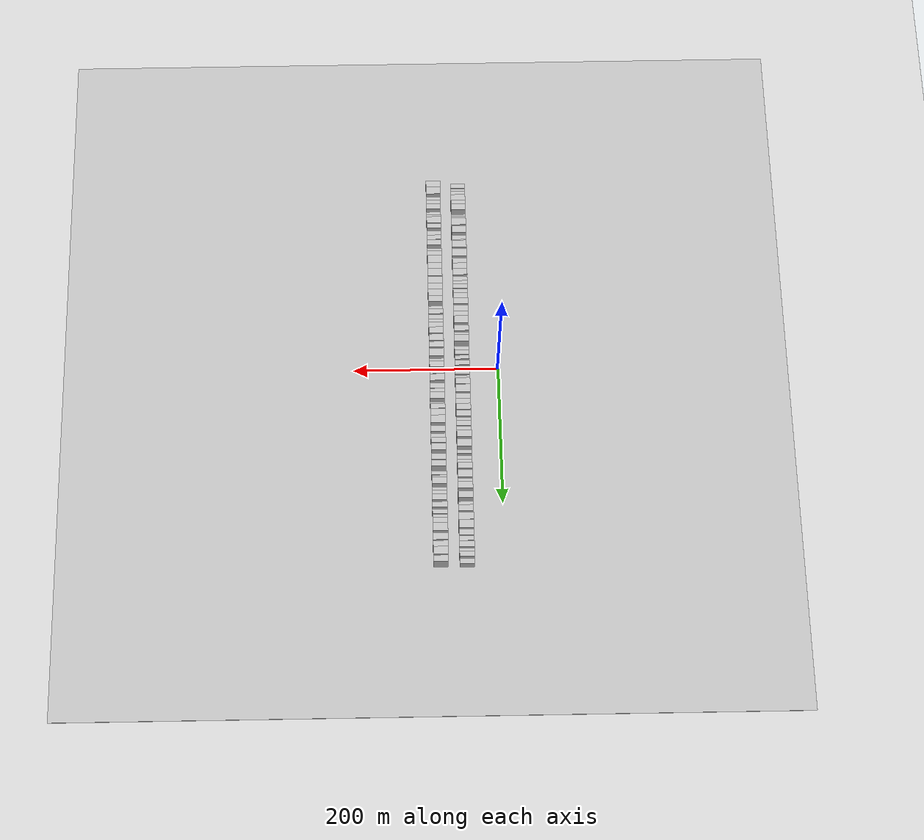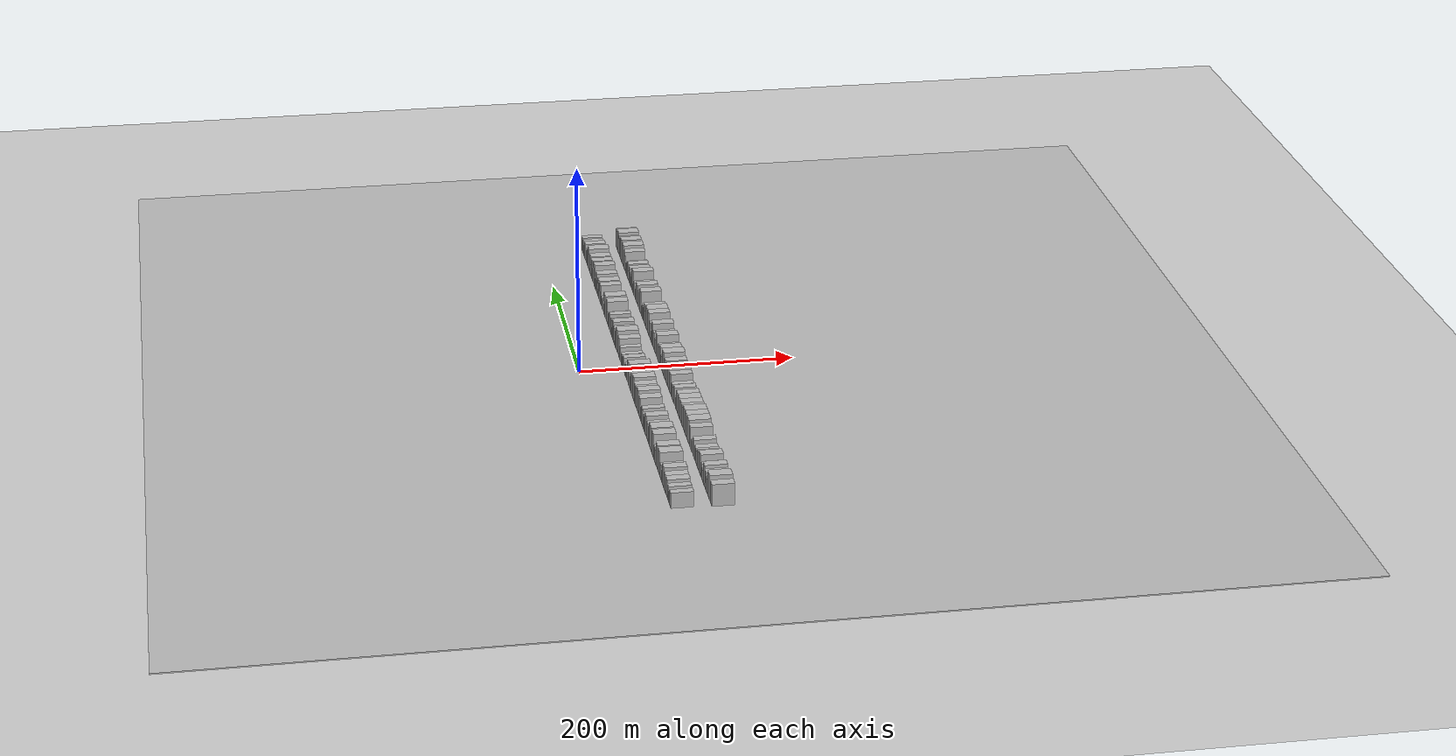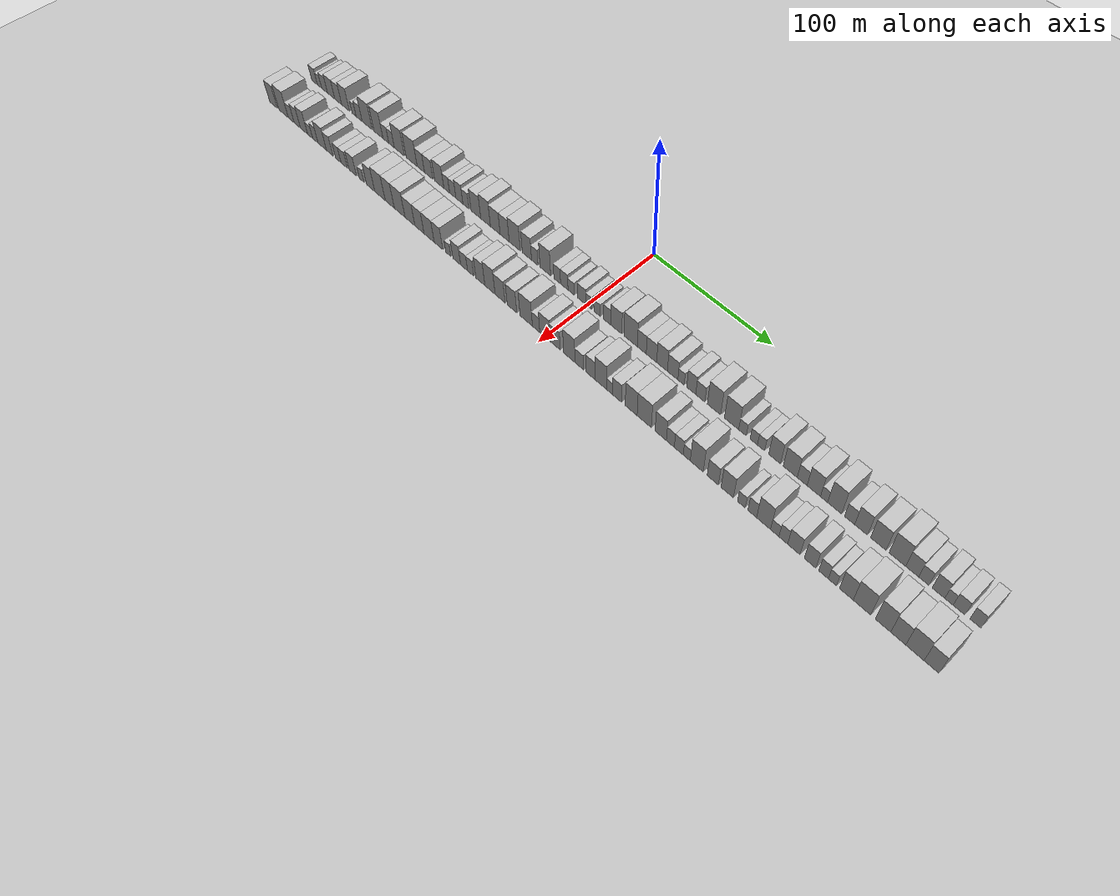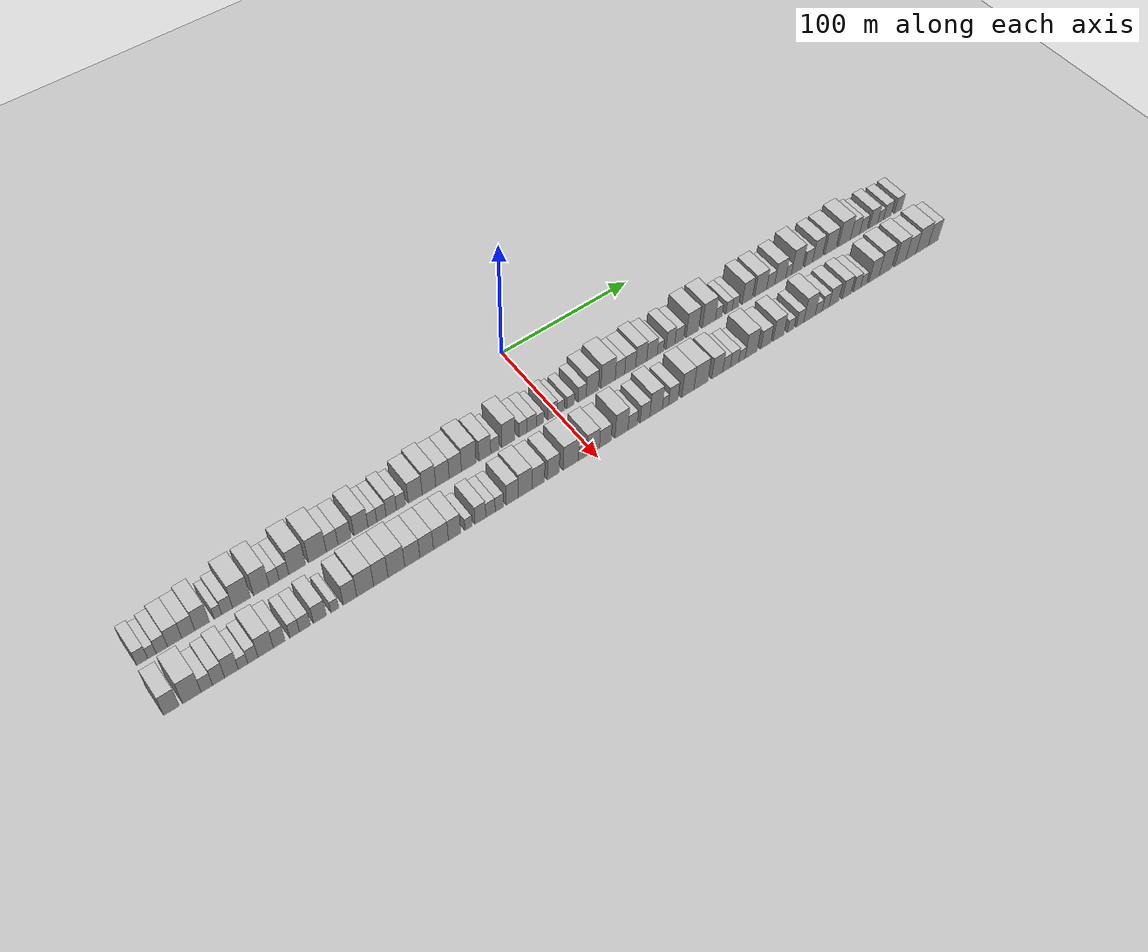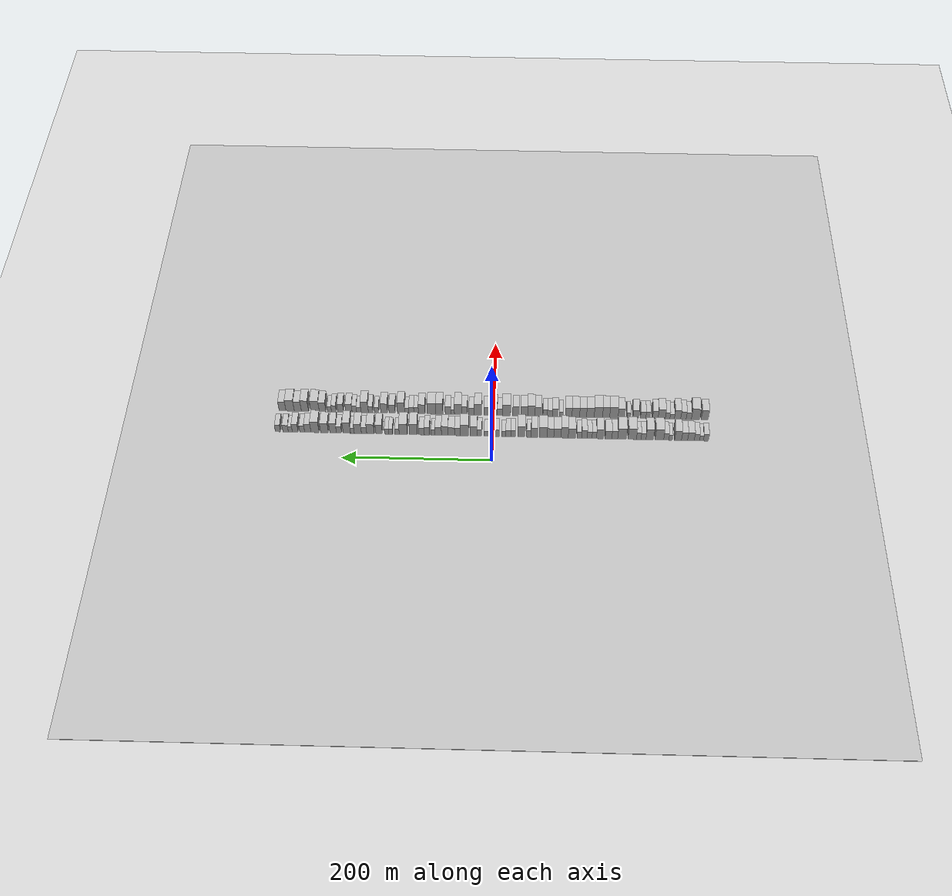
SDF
<?xml version="1.0" encoding="utf-8"?>

<sdf version="1.6">

   <world name="default">

      <gui fullscreen="0">

         <camera name="user_camera">

            <pose>-15 0 4.57585 0 0 0</pose>

            <view_controller>orbit</view_controller>

         </camera>

      </gui>

      <scene>

         <sky>

           <clouds>

             <speed>12</speed>

           </clouds>

         </sky>

         <ambient>0.4 0.4 0.4 1</ambient>

         <background>0.7 0.7 0.7 1</background>

         <shadows>1</shadows>

      </scene>

      <gravity>0 0 -9.8066</gravity>

      <magnetic_field>6e-06 2.3e-05 -4.2e-05</magnetic_field>

      <physics default="0" name="default_physics" type="ode">

         <ode>

            <solver>

               <type>quick</type>

               <iters>10</iters>

               <sor>1.0</sor>

               <use_dynamic_moi_rescaling>0</use_dynamic_moi_rescaling>

            </solver>

            <constraints>

               <cfm>0</cfm>

               <erp>0.2</erp>

               <contact_max_correcting_vel>100</contact_max_correcting_vel>

               <contact_surface_layer>0.001</contact_surface_layer>

            </constraints>

         </ode>

         <max_step_size>0.004</max_step_size>

         <real_time_factor>1</real_time_factor>

         <real_time_update_rate>250</real_time_update_rate>

      </physics>

      <light name="sun" type="directional">

         <cast_shadows>1</cast_shadows>

         <pose>0 0 10 0 0 0</pose>

         <diffuse>0.8 0.8 0.8 1</diffuse>

         <specular>0.2 0.2 0.2 1</specular>

         <attenuation>

            <range>1000</range>

            <constant>0.9</constant>

            <linear>0.01</linear>

            <quadratic>0.001</quadratic>

         </attenuation>

         <direction>-0.5 0.1 -0.9</direction>

      </light>

      <include>

         <name>ground_plane_1</name>

         <uri>model://HANNAS_ground_plane</uri>

         <pose>0 0 0  0 0 0</pose>

      </include>

      <include>

         <name>ground_plane_2</name>

         <uri>model://HANNAS_ground_plane</uri>

         <pose>100 0 0  0 0 0</pose>

      </include>

      <model name="building_1">

         <static>1</static>

         <pose frame="">50.0000 -284.5812 0 0.000000 0.000000 0.000000</pose>

         <link name="link">

            <pose frame="">0 0 7.50 0 0 0</pose>

            <collision name="collision">

               <geometry>

                  <box>

                     <size>20.0000 6.8375 15.0000</size>

                  </box>

               </geometry>

               <max_contacts>10</max_contacts>

               <surface>

                  <contact>

                     <ode/>

                  </contact>

                  <bounce/>

                  <friction>

                     <torsional>

                        <ode/>

                     </torsional>

                     <ode/>

                  </friction>

               </surface>

            </collision>

            <visual name="visual">

               <cast_shadows>0</cast_shadows>

               <geometry>

                  <box>

                     <size>20.0000 6.8375 15.0000</size>

                  </box>

               </geometry>

               <material>

                  <script>

                     <uri>model://HANNAS_wall/materials/scripts</uri>

                     <uri>model://HANNAS_wall/materials/textures</uri>

                     <name>vrc/HANNAS_wall</name>

                  </script>

               </material>

            </visual>

            <self_collide>0</self_collide>

            <enable_wind>0</enable_wind>

            <kinematic>0</kinematic>

         </link>

      </model>

      <model name="building_2">

         <static>1</static>

         <pose frame="">50.0000 -278.5755 0 0.000000 0.000000 0.000000</pose>

         <link name="link">

            <pose frame="">0 0 6.00 0 0 0</pose>

            <collision name="collision">

               <geometry>

                  <box>

                     <size>20.0000 5.1739 12.0000</size>

                  </box>

               </geometry>

               <max_contacts>10</max_contacts>

               <surface>

                  <contact>

                     <ode/>

                  </contact>

                  <bounce/>

                  <friction>

                     <torsional>

                        <ode/>

                     </torsional>

                     <ode/>

                  </friction>

               </surface>

            </collision>

            <visual name="visual">

               <cast_shadows>0</cast_shadows>

               <geometry>

                  <box>

                     <size>20.0000 5.1739 12.0000</size>

                  </box>

               </geometry>

               <material>

                  <script>

                     <uri>model://HANNAS_wall/materials/scripts</uri>

                     <uri>model://HANNAS_wall/materials/textures</uri>

                     <name>vrc/HANNAS_wall</name>

                  </script>

               </material>

            </visual>

            <self_collide>0</self_collide>

            <enable_wind>0</enable_wind>

            <kinematic>0</kinematic>

         </link>

      </model>

      <model name="building_3">

         <static>1</static>

         <pose frame="">50.0000 -272.4945 0 0.000000 0.000000 0.000000</pose>

         <link name="link">

            <pose frame="">0 0 7.50 0 0 0</pose>

            <collision name="collision">

               <geometry>

                  <box>

                     <size>20.0000 6.9881 15.0000</size>

                  </box>

               </geometry>

               <max_contacts>10</max_contacts>

               <surface>

                  <contact>

                     <ode/>

                  </contact>

                  <bounce/>

                  <friction>

                     <torsional>

                        <ode/>

                     </torsional>

                     <ode/>

                  </friction>

               </surface>

            </collision>

            <visual name="visual">

               <cast_shadows>0</cast_shadows>

               <geometry>

                  <box>

                     <size>20.0000 6.9881 15.0000</size>

                  </box>

               </geometry>

               <material>

                  <script>

                     <uri>model://HANNAS_wall/materials/scripts</uri>

                     <uri>model://HANNAS_wall/materials/textures</uri>

                     <name>vrc/HANNAS_wall</name>

                  </script>

               </material>

            </visual>

            <self_collide>0</self_collide>

            <enable_wind>0</enable_wind>

            <kinematic>0</kinematic>

         </link>

      </model>

      <model name="building_4">

         <static>1</static>

         <pose frame="">50.0000 -264.5793 0 0.000000 0.000000 0.000000</pose>

         <link name="link">

            <pose frame="">0 0 9.00 0 0 0</pose>

            <collision name="collision">

               <geometry>

                  <box>

                     <size>20.0000 8.8423 18.0000</size>

                  </box>

               </geometry>

               <max_contacts>10</max_contacts>

               <surface>

                  <contact>

                     <ode/>

                  </contact>

                  <bounce/>

                  <friction>

                     <torsional>

                        <ode/>

                     </torsional>

                     <ode/>

                  </friction>

               </surface>

            </collision>

            <visual name="visual">

               <cast_shadows>0</cast_shadows>

               <geometry>

                  <box>

                     <size>20.0000 8.8423 18.0000</size>

                  </box>

               </geometry>

               <material>

                  <script>

                     <uri>model://HANNAS_wall/materials/scripts</uri>

                     <uri>model://HANNAS_wall/materials/textures</uri>

                     <name>vrc/HANNAS_wall</name>

                  </script>

               </material>

            </visual>

            <self_collide>0</self_collide>

            <enable_wind>0</enable_wind>

            <kinematic>0</kinematic>

         </link>

      </model>

      <model name="building_5">

         <static>1</static>

         <pose frame="">50.0000 -256.0554 0 0.000000 0.000000 0.000000</pose>

         <link name="link">

            <pose frame="">0 0 9.00 0 0 0</pose>

            <collision name="collision">

               <geometry>

                  <box>

                     <size>20.0000 8.2054 18.0000</size>

                  </box>

               </geometry>

               <max_contacts>10</max_contacts>

               <surface>

                  <contact>

                     <ode/>

                  </contact>

                  <bounce/>

                  <friction>

                     <torsional>

                        <ode/>

                     </torsional>

                     <ode/>

                  </friction>

               </surface>

            </collision>

            <visual name="visual">

               <cast_shadows>0</cast_shadows>

               <geometry>

                  <box>

                     <size>20.0000 8.2054 18.0000</size>

                  </box>

               </geometry>

               <material>

                  <script>

                     <uri>model://HANNAS_wall/materials/scripts</uri>

                     <uri>model://HANNAS_wall/materials/textures</uri>

                     <name>vrc/HANNAS_wall</name>

                  </script>

               </material>

            </visual>

            <self_collide>0</self_collide>

            <enable_wind>0</enable_wind>

            <kinematic>0</kinematic>

         </link>

      </model>

      <model name="building_6">

         <static>1</static>

         <pose frame="">50.0000 -247.4107 0 0.000000 0.000000 0.000000</pose>

         <link name="link">

            <pose frame="">0 0 10.50 0 0 0</pose>

            <collision name="collision">

               <geometry>

                  <box>

                     <size>20.0000 9.0841 21.0000</size>

                  </box>

               </geometry>

               <max_contacts>10</max_contacts>

               <surface>

                  <contact>

                     <ode/>

                  </contact>

                  <bounce/>

                  <friction>

                     <torsional>

                        <ode/>

                     </torsional>

                     <ode/>

                  </friction>

               </surface>

            </collision>

            <visual name="visual">

               <cast_shadows>0</cast_shadows>

               <geometry>

                  <box>

                     <size>20.0000 9.0841 21.0000</size>

                  </box>

               </geometry>

               <material>

                  <script>

                     <uri>model://HANNAS_wall/materials/scripts</uri>

                     <uri>model://HANNAS_wall/materials/textures</uri>

                     <name>vrc/HANNAS_wall</name>

                  </script>

               </material>

            </visual>

            <self_collide>0</self_collide>

            <enable_wind>0</enable_wind>

            <kinematic>0</kinematic>

         </link>

      </model>

      <model name="building_7">

         <static>1</static>

         <pose frame="">50.0000 -237.4643 0 0.000000 0.000000 0.000000</pose>

         <link name="link">

            <pose frame="">0 0 6.00 0 0 0</pose>

            <collision name="collision">

               <geometry>

                  <box>

                     <size>20.0000 4.8087 12.0000</size>

                  </box>

               </geometry>

               <max_contacts>10</max_contacts>

               <surface>

                  <contact>

                     <ode/>

                  </contact>

                  <bounce/>

                  <friction>

                     <torsional>

                        <ode/>

                     </torsional>

                     <ode/>

                  </friction>

               </surface>

            </collision>

            <visual name="visual">

               <cast_shadows>0</cast_shadows>

               <geometry>

                  <box>

                     <size>20.0000 4.8087 12.0000</size>

                  </box>

               </geometry>

               <material>

                  <script>

                     <uri>model://HANNAS_wall/materials/scripts</uri>

                     <uri>model://HANNAS_wall/materials/textures</uri>

                     <name>vrc/HANNAS_wall</name>

                  </script>

               </material>

            </visual>

            <self_collide>0</self_collide>

            <enable_wind>0</enable_wind>

            <kinematic>0</kinematic>

         </link>

      </model>

      <model name="building_8">

         <static>1</static>

         <pose frame="">50.0000 -231.5951 0 0.000000 0.000000 0.000000</pose>

         <link name="link">

            <pose frame="">0 0 7.50 0 0 0</pose>

            <collision name="collision">

               <geometry>

                  <box>

                     <size>20.0000 6.9297 15.0000</size>

                  </box>

               </geometry>

               <max_contacts>10</max_contacts>

               <surface>

                  <contact>

                     <ode/>

                  </contact>

                  <bounce/>

                  <friction>

                     <torsional>

                        <ode/>

                     </torsional>

                     <ode/>

                  </friction>

               </surface>

            </collision>

            <visual name="visual">

               <cast_shadows>0</cast_shadows>

               <geometry>

                  <box>

                     <size>20.0000 6.9297 15.0000</size>

                  </box>

               </geometry>

               <material>

                  <script>

                     <uri>model://HANNAS_wall/materials/scripts</uri>

                     <uri>model://HANNAS_wall/materials/textures</uri>

                     <name>vrc/HANNAS_wall</name>

                  </script>

               </material>

            </visual>

            <self_collide>0</self_collide>

            <enable_wind>0</enable_wind>

            <kinematic>0</kinematic>

         </link>

      </model>

      <model name="building_9">

         <static>1</static>

         <pose frame="">50.0000 -222.3538 0 0.000000 0.000000 0.000000</pose>

         <link name="link">

            <pose frame="">0 0 12.00 0 0 0</pose>

            <collision name="collision">

               <geometry>

                  <box>

                     <size>20.0000 11.5530 24.0000</size>

                  </box>

               </geometry>

               <max_contacts>10</max_contacts>

               <surface>

                  <contact>

                     <ode/>

                  </contact>

                  <bounce/>

                  <friction>

                     <torsional>

                        <ode/>

                     </torsional>

                     <ode/>

                  </friction>

               </surface>

            </collision>

            <visual name="visual">

               <cast_shadows>0</cast_shadows>

               <geometry>

                  <box>

                     <size>20.0000 11.5530 24.0000</size>

                  </box>

               </geometry>

               <material>

                  <script>

                     <uri>model://HANNAS_wall/materials/scripts</uri>

                     <uri>model://HANNAS_wall/materials/textures</uri>

                     <name>vrc/HANNAS_wall</name>

                  </script>

               </material>

            </visual>

            <self_collide>0</self_collide>

            <enable_wind>0</enable_wind>

            <kinematic>0</kinematic>

         </link>

      </model>

      <model name="building_10">

         <static>1</static>

         <pose frame="">50.0000 -209.5118 0 0.000000 0.000000 0.000000</pose>

         <link name="link">

            <pose frame="">0 0 12.00 0 0 0</pose>

            <collision name="collision">

               <geometry>

                  <box>

                     <size>20.0000 10.1310 24.0000</size>

                  </box>

               </geometry>

               <max_contacts>10</max_contacts>

               <surface>

                  <contact>

                     <ode/>

                  </contact>

                  <bounce/>

                  <friction>

                     <torsional>

                        <ode/>

                     </torsional>

                     <ode/>

                  </friction>

               </surface>

            </collision>

            <visual name="visual">

               <cast_shadows>0</cast_shadows>

               <geometry>

                  <box>

                     <size>20.0000 10.1310 24.0000</size>

                  </box>

               </geometry>

               <material>

                  <script>

                     <uri>model://HANNAS_wall/materials/scripts</uri>

                     <uri>model://HANNAS_wall/materials/textures</uri>

                     <name>vrc/HANNAS_wall</name>

                  </script>

               </material>

            </visual>

            <self_collide>0</self_collide>

            <enable_wind>0</enable_wind>

            <kinematic>0</kinematic>

         </link>

      </model>

      <model name="building_11">

         <static>1</static>

         <pose frame="">50.0000 -201.1708 0 0.000000 0.000000 0.000000</pose>

         <link name="link">

            <pose frame="">0 0 7.50 0 0 0</pose>

            <collision name="collision">

               <geometry>

                  <box>

                     <size>20.0000 6.5511 15.0000</size>

                  </box>

               </geometry>

               <max_contacts>10</max_contacts>

               <surface>

                  <contact>

                     <ode/>

                  </contact>

                  <bounce/>

                  <friction>

                     <torsional>

                        <ode/>

                     </torsional>

                     <ode/>

                  </friction>

               </surface>

            </collision>

            <visual name="visual">

               <cast_shadows>0</cast_shadows>

               <geometry>

                  <box>

                     <size>20.0000 6.5511 15.0000</size>

                  </box>

               </geometry>

               <material>

                  <script>

                     <uri>model://HANNAS_wall/materials/scripts</uri>

                     <uri>model://HANNAS_wall/materials/textures</uri>

                     <name>vrc/HANNAS_wall</name>

                  </script>

               </material>

            </visual>

            <self_collide>0</self_collide>

            <enable_wind>0</enable_wind>

            <kinematic>0</kinematic>

         </link>

      </model>

      <model name="building_12">

         <static>1</static>

         <pose frame="">50.0000 -194.7943 0 0.000000 0.000000 0.000000</pose>

         <link name="link">

            <pose frame="">0 0 7.50 0 0 0</pose>

            <collision name="collision">

               <geometry>

                  <box>

                     <size>20.0000 6.2018 15.0000</size>

                  </box>

               </geometry>

               <max_contacts>10</max_contacts>

               <surface>

                  <contact>

                     <ode/>

                  </contact>

                  <bounce/>

                  <friction>

                     <torsional>

                        <ode/>

                     </torsional>

                     <ode/>

                  </friction>

               </surface>

            </collision>

            <visual name="visual">

               <cast_shadows>0</cast_shadows>

               <geometry>

                  <box>

                     <size>20.0000 6.2018 15.0000</size>

                  </box>

               </geometry>

               <material>

                  <script>

                     <uri>model://HANNAS_wall/materials/scripts</uri>

                     <uri>model://HANNAS_wall/materials/textures</uri>

                     <name>vrc/HANNAS_wall</name>

                  </script>

               </material>

            </visual>

            <self_collide>0</self_collide>

            <enable_wind>0</enable_wind>

            <kinematic>0</kinematic>

         </link>

      </model>

      <model name="building_13">

         <static>1</static>

         <pose frame="">50.0000 -186.1245 0 0.000000 0.000000 0.000000</pose>

         <link name="link">

            <pose frame="">0 0 12.00 0 0 0</pose>

            <collision name="collision">

               <geometry>

                  <box>

                     <size>20.0000 11.1378 24.0000</size>

                  </box>

               </geometry>

               <max_contacts>10</max_contacts>

               <surface>

                  <contact>

                     <ode/>

                  </contact>

                  <bounce/>

                  <friction>

                     <torsional>

                        <ode/>

                     </torsional>

                     <ode/>

                  </friction>

               </surface>

            </collision>

            <visual name="visual">

               <cast_shadows>0</cast_shadows>

               <geometry>

                  <box>

                     <size>20.0000 11.1378 24.0000</size>

                  </box>

               </geometry>

               <material>

                  <script>

                     <uri>model://HANNAS_wall/materials/scripts</uri>

                     <uri>model://HANNAS_wall/materials/textures</uri>

                     <name>vrc/HANNAS_wall</name>

                  </script>

               </material>

            </visual>

            <self_collide>0</self_collide>

            <enable_wind>0</enable_wind>

            <kinematic>0</kinematic>

         </link>

      </model>

      <model name="building_14">

         <static>1</static>

         <pose frame="">50.0000 -172.6004 0 0.000000 0.000000 0.000000</pose>

         <link name="link">

            <pose frame="">0 0 12.00 0 0 0</pose>

            <collision name="collision">

               <geometry>

                  <box>

                     <size>20.0000 11.9105 24.0000</size>

                  </box>

               </geometry>

               <max_contacts>10</max_contacts>

               <surface>

                  <contact>

                     <ode/>

                  </contact>

                  <bounce/>

                  <friction>

                     <torsional>

                        <ode/>

                     </torsional>

                     <ode/>

                  </friction>

               </surface>

            </collision>

            <visual name="visual">

               <cast_shadows>0</cast_shadows>

               <geometry>

                  <box>

                     <size>20.0000 11.9105 24.0000</size>

                  </box>

               </geometry>

               <material>

                  <script>

                     <uri>model://HANNAS_wall/materials/scripts</uri>

                     <uri>model://HANNAS_wall/materials/textures</uri>

                     <name>vrc/HANNAS_wall</name>

                  </script>

               </material>

            </visual>

            <self_collide>0</self_collide>

            <enable_wind>0</enable_wind>

            <kinematic>0</kinematic>

         </link>

      </model>

      <model name="building_15">

         <static>1</static>

         <pose frame="">50.0000 -162.6880 0 0.000000 0.000000 0.000000</pose>

         <link name="link">

            <pose frame="">0 0 9.00 0 0 0</pose>

            <collision name="collision">

               <geometry>

                  <box>

                     <size>20.0000 7.9143 18.0000</size>

                  </box>

               </geometry>

               <max_contacts>10</max_contacts>

               <surface>

                  <contact>

                     <ode/>

                  </contact>

                  <bounce/>

                  <friction>

                     <torsional>

                        <ode/>

                     </torsional>

                     <ode/>

                  </friction>

               </surface>

            </collision>

            <visual name="visual">

               <cast_shadows>0</cast_shadows>

               <geometry>

                  <box>

                     <size>20.0000 7.9143 18.0000</size>

                  </box>

               </geometry>

               <material>

                  <script>

                     <uri>model://HANNAS_wall/materials/scripts</uri>

                     <uri>model://HANNAS_wall/materials/textures</uri>

                     <name>vrc/HANNAS_wall</name>

                  </script>

               </material>

            </visual>

            <self_collide>0</self_collide>

            <enable_wind>0</enable_wind>

            <kinematic>0</kinematic>

         </link>

      </model>

      <model name="building_16">

         <static>1</static>

         <pose frame="">50.0000 -154.3279 0 0.000000 0.000000 0.000000</pose>

         <link name="link">

            <pose frame="">0 0 9.00 0 0 0</pose>

            <collision name="collision">

               <geometry>

                  <box>

                     <size>20.0000 8.8059 18.0000</size>

                  </box>

               </geometry>

               <max_contacts>10</max_contacts>

               <surface>

                  <contact>

                     <ode/>

                  </contact>

                  <bounce/>

                  <friction>

                     <torsional>

                        <ode/>

                     </torsional>

                     <ode/>

                  </friction>

               </surface>

            </collision>

            <visual name="visual">

               <cast_shadows>0</cast_shadows>

               <geometry>

                  <box>

                     <size>20.0000 8.8059 18.0000</size>

                  </box>

               </geometry>

               <material>

                  <script>

                     <uri>model://HANNAS_wall/materials/scripts</uri>

                     <uri>model://HANNAS_wall/materials/textures</uri>

                     <name>vrc/HANNAS_wall</name>

                  </script>

               </material>

            </visual>

            <self_collide>0</self_collide>

            <enable_wind>0</enable_wind>

            <kinematic>0</kinematic>

         </link>

      </model>

      <model name="building_17">

         <static>1</static>

         <pose frame="">50.0000 -143.1177 0 0.000000 0.000000 0.000000</pose>

         <link name="link">

            <pose frame="">0 0 10.50 0 0 0</pose>

            <collision name="collision">

               <geometry>

                  <box>

                     <size>20.0000 9.6144 21.0000</size>

                  </box>

               </geometry>

               <max_contacts>10</max_contacts>

               <surface>

                  <contact>

                     <ode/>

                  </contact>

                  <bounce/>

                  <friction>

                     <torsional>

                        <ode/>

                     </torsional>

                     <ode/>

                  </friction>

               </surface>

            </collision>

            <visual name="visual">

               <cast_shadows>0</cast_shadows>

               <geometry>

                  <box>

                     <size>20.0000 9.6144 21.0000</size>

                  </box>

               </geometry>

               <material>

                  <script>

                     <uri>model://HANNAS_wall/materials/scripts</uri>

                     <uri>model://HANNAS_wall/materials/textures</uri>

                     <name>vrc/HANNAS_wall</name>

                  </script>

               </material>

            </visual>

            <self_collide>0</self_collide>

            <enable_wind>0</enable_wind>

            <kinematic>0</kinematic>

         </link>

      </model>

      <model name="building_18">

         <static>1</static>

         <pose frame="">50.0000 -135.2743 0 0.000000 0.000000 0.000000</pose>

         <link name="link">

            <pose frame="">0 0 7.50 0 0 0</pose>

            <collision name="collision">

               <geometry>

                  <box>

                     <size>20.0000 6.0724 15.0000</size>

                  </box>

               </geometry>

               <max_contacts>10</max_contacts>

               <surface>

                  <contact>

                     <ode/>

                  </contact>

                  <bounce/>

                  <friction>

                     <torsional>

                        <ode/>

                     </torsional>

                     <ode/>

                  </friction>

               </surface>

            </collision>

            <visual name="visual">

               <cast_shadows>0</cast_shadows>

               <geometry>

                  <box>

                     <size>20.0000 6.0724 15.0000</size>

                  </box>

               </geometry>

               <material>

                  <script>

                     <uri>model://HANNAS_wall/materials/scripts</uri>

                     <uri>model://HANNAS_wall/materials/textures</uri>

                     <name>vrc/HANNAS_wall</name>

                  </script>

               </material>

            </visual>

            <self_collide>0</self_collide>

            <enable_wind>0</enable_wind>

            <kinematic>0</kinematic>

         </link>

      </model>

      <model name="building_19">

         <static>1</static>

         <pose frame="">50.0000 -129.0100 0 0.000000 0.000000 0.000000</pose>

         <link name="link">

            <pose frame="">0 0 7.50 0 0 0</pose>

            <collision name="collision">

               <geometry>

                  <box>

                     <size>20.0000 6.4562 15.0000</size>

                  </box>

               </geometry>

               <max_contacts>10</max_contacts>

               <surface>

                  <contact>

                     <ode/>

                  </contact>

                  <bounce/>

                  <friction>

                     <torsional>

                        <ode/>

                     </torsional>

                     <ode/>

                  </friction>

               </surface>

            </collision>

            <visual name="visual">

               <cast_shadows>0</cast_shadows>

               <geometry>

                  <box>

                     <size>20.0000 6.4562 15.0000</size>

                  </box>

               </geometry>

               <material>

                  <script>

                     <uri>model://HANNAS_wall/materials/scripts</uri>

                     <uri>model://HANNAS_wall/materials/textures</uri>

                     <name>vrc/HANNAS_wall</name>

                  </script>

               </material>

            </visual>

            <self_collide>0</self_collide>

            <enable_wind>0</enable_wind>

            <kinematic>0</kinematic>

         </link>

      </model>

      <model name="building_20">

         <static>1</static>

         <pose frame="">50.0000 -122.1704 0 0.000000 0.000000 0.000000</pose>

         <link name="link">

            <pose frame="">0 0 9.00 0 0 0</pose>

            <collision name="collision">

               <geometry>

                  <box>

                     <size>20.0000 7.2230 18.0000</size>

                  </box>

               </geometry>

               <max_contacts>10</max_contacts>

               <surface>

                  <contact>

                     <ode/>

                  </contact>

                  <bounce/>

                  <friction>

                     <torsional>

                        <ode/>

                     </torsional>

                     <ode/>

                  </friction>

               </surface>

            </collision>

            <visual name="visual">

               <cast_shadows>0</cast_shadows>

               <geometry>

                  <box>

                     <size>20.0000 7.2230 18.0000</size>

                  </box>

               </geometry>

               <material>

                  <script>

                     <uri>model://HANNAS_wall/materials/scripts</uri>

                     <uri>model://HANNAS_wall/materials/textures</uri>

                     <name>vrc/HANNAS_wall</name>

                  </script>

               </material>

            </visual>

            <self_collide>0</self_collide>

            <enable_wind>0</enable_wind>

            <kinematic>0</kinematic>

         </link>

      </model>

      <model name="building_21">

         <static>1</static>

         <pose frame="">50.0000 -115.4104 0 0.000000 0.000000 0.000000</pose>

         <link name="link">

            <pose frame="">0 0 7.50 0 0 0</pose>

            <collision name="collision">

               <geometry>

                  <box>

                     <size>20.0000 6.2971 15.0000</size>

                  </box>

               </geometry>

               <max_contacts>10</max_contacts>

               <surface>

                  <contact>

                     <ode/>

                  </contact>

                  <bounce/>

                  <friction>

                     <torsional>

                        <ode/>

                     </torsional>

                     <ode/>

                  </friction>

               </surface>

            </collision>

            <visual name="visual">

               <cast_shadows>0</cast_shadows>

               <geometry>

                  <box>

                     <size>20.0000 6.2971 15.0000</size>

                  </box>

               </geometry>

               <material>

                  <script>

                     <uri>model://HANNAS_wall/materials/scripts</uri>

                     <uri>model://HANNAS_wall/materials/textures</uri>

                     <name>vrc/HANNAS_wall</name>

                  </script>

               </material>

            </visual>

            <self_collide>0</self_collide>

            <enable_wind>0</enable_wind>

            <kinematic>0</kinematic>

         </link>

      </model>

      <model name="building_22">

         <static>1</static>

         <pose frame="">50.0000 -105.3460 0 0.000000 0.000000 0.000000</pose>

         <link name="link">

            <pose frame="">0 0 10.50 0 0 0</pose>

            <collision name="collision">

               <geometry>

                  <box>

                     <size>20.0000 9.8316 21.0000</size>

                  </box>

               </geometry>

               <max_contacts>10</max_contacts>

               <surface>

                  <contact>

                     <ode/>

                  </contact>

                  <bounce/>

                  <friction>

                     <torsional>

                        <ode/>

                     </torsional>

                     <ode/>

                  </friction>

               </surface>

            </collision>

            <visual name="visual">

               <cast_shadows>0</cast_shadows>

               <geometry>

                  <box>

                     <size>20.0000 9.8316 21.0000</size>

                  </box>

               </geometry>

               <material>

                  <script>

                     <uri>model://HANNAS_wall/materials/scripts</uri>

                     <uri>model://HANNAS_wall/materials/textures</uri>

                     <name>vrc/HANNAS_wall</name>

                  </script>

               </material>

            </visual>

            <self_collide>0</self_collide>

            <enable_wind>0</enable_wind>

            <kinematic>0</kinematic>

         </link>

      </model>

      <model name="building_23">

         <static>1</static>

         <pose frame="">50.0000 -95.6116 0 0.000000 0.000000 0.000000</pose>

         <link name="link">

            <pose frame="">0 0 12.00 0 0 0</pose>

            <collision name="collision">

               <geometry>

                  <box>

                     <size>20.0000 9.6372 24.0000</size>

                  </box>

               </geometry>

               <max_contacts>10</max_contacts>

               <surface>

                  <contact>

                     <ode/>

                  </contact>

                  <bounce/>

                  <friction>

                     <torsional>

                        <ode/>

                     </torsional>

                     <ode/>

                  </friction>

               </surface>

            </collision>

            <visual name="visual">

               <cast_shadows>0</cast_shadows>

               <geometry>

                  <box>

                     <size>20.0000 9.6372 24.0000</size>

                  </box>

               </geometry>

               <material>

                  <script>

                     <uri>model://HANNAS_wall/materials/scripts</uri>

                     <uri>model://HANNAS_wall/materials/textures</uri>

                     <name>vrc/HANNAS_wall</name>

                  </script>

               </material>

            </visual>

            <self_collide>0</self_collide>

            <enable_wind>0</enable_wind>

            <kinematic>0</kinematic>

         </link>

      </model>

      <model name="building_24">

         <static>1</static>

         <pose frame="">50.0000 -85.9801 0 0.000000 0.000000 0.000000</pose>

         <link name="link">

            <pose frame="">0 0 10.50 0 0 0</pose>

            <collision name="collision">

               <geometry>

                  <box>

                     <size>20.0000 9.6257 21.0000</size>

                  </box>

               </geometry>

               <max_contacts>10</max_contacts>

               <surface>

                  <contact>

                     <ode/>

                  </contact>

                  <bounce/>

                  <friction>

                     <torsional>

                        <ode/>

                     </torsional>

                     <ode/>

                  </friction>

               </surface>

            </collision>

            <visual name="visual">

               <cast_shadows>0</cast_shadows>

               <geometry>

                  <box>

                     <size>20.0000 9.6257 21.0000</size>

                  </box>

               </geometry>

               <material>

                  <script>

                     <uri>model://HANNAS_wall/materials/scripts</uri>

                     <uri>model://HANNAS_wall/materials/textures</uri>

                     <name>vrc/HANNAS_wall</name>

                  </script>

               </material>

            </visual>

            <self_collide>0</self_collide>

            <enable_wind>0</enable_wind>

            <kinematic>0</kinematic>

         </link>

      </model>

      <model name="building_25">

         <static>1</static>

         <pose frame="">50.0000 -76.7564 0 0.000000 0.000000 0.000000</pose>

         <link name="link">

            <pose frame="">0 0 10.50 0 0 0</pose>

            <collision name="collision">

               <geometry>

                  <box>

                     <size>20.0000 8.8217 21.0000</size>

                  </box>

               </geometry>

               <max_contacts>10</max_contacts>

               <surface>

                  <contact>

                     <ode/>

                  </contact>

                  <bounce/>

                  <friction>

                     <torsional>

                        <ode/>

                     </torsional>

                     <ode/>

                  </friction>

               </surface>

            </collision>

            <visual name="visual">

               <cast_shadows>0</cast_shadows>

               <geometry>

                  <box>

                     <size>20.0000 8.8217 21.0000</size>

                  </box>

               </geometry>

               <material>

                  <script>

                     <uri>model://HANNAS_wall/materials/scripts</uri>

                     <uri>model://HANNAS_wall/materials/textures</uri>

                     <name>vrc/HANNAS_wall</name>

                  </script>

               </material>

            </visual>

            <self_collide>0</self_collide>

            <enable_wind>0</enable_wind>

            <kinematic>0</kinematic>

         </link>

      </model>

      <model name="building_26">

         <static>1</static>

         <pose frame="">50.0000 -66.9950 0 0.000000 0.000000 0.000000</pose>

         <link name="link">

            <pose frame="">0 0 12.00 0 0 0</pose>

            <collision name="collision">

               <geometry>

                  <box>

                     <size>20.0000 10.7010 24.0000</size>

                  </box>

               </geometry>

               <max_contacts>10</max_contacts>

               <surface>

                  <contact>

                     <ode/>

                  </contact>

                  <bounce/>

                  <friction>

                     <torsional>

                        <ode/>

                     </torsional>

                     <ode/>

                  </friction>

               </surface>

            </collision>

            <visual name="visual">

               <cast_shadows>0</cast_shadows>

               <geometry>

                  <box>

                     <size>20.0000 10.7010 24.0000</size>

                  </box>

               </geometry>

               <material>

                  <script>

                     <uri>model://HANNAS_wall/materials/scripts</uri>

                     <uri>model://HANNAS_wall/materials/textures</uri>

                     <name>vrc/HANNAS_wall</name>

                  </script>

               </material>

            </visual>

            <self_collide>0</self_collide>

            <enable_wind>0</enable_wind>

            <kinematic>0</kinematic>

         </link>

      </model>

      <model name="building_27">

         <static>1</static>

         <pose frame="">50.0000 -55.2342 0 0.000000 0.000000 0.000000</pose>

         <link name="link">

            <pose frame="">0 0 10.50 0 0 0</pose>

            <collision name="collision">

               <geometry>

                  <box>

                     <size>20.0000 8.8207 21.0000</size>

                  </box>

               </geometry>

               <max_contacts>10</max_contacts>

               <surface>

                  <contact>

                     <ode/>

                  </contact>

                  <bounce/>

                  <friction>

                     <torsional>

                        <ode/>

                     </torsional>

                     <ode/>

                  </friction>

               </surface>

            </collision>

            <visual name="visual">

               <cast_shadows>0</cast_shadows>

               <geometry>

                  <box>

                     <size>20.0000 8.8207 21.0000</size>

                  </box>

               </geometry>

               <material>

                  <script>

                     <uri>model://HANNAS_wall/materials/scripts</uri>

                     <uri>model://HANNAS_wall/materials/textures</uri>

                     <name>vrc/HANNAS_wall</name>

                  </script>

               </material>

            </visual>

            <self_collide>0</self_collide>

            <enable_wind>0</enable_wind>

            <kinematic>0</kinematic>

         </link>

      </model>

      <model name="building_28">

         <static>1</static>

         <pose frame="">50.0000 -47.8002 0 0.000000 0.000000 0.000000</pose>

         <link name="link">

            <pose frame="">0 0 7.50 0 0 0</pose>

            <collision name="collision">

               <geometry>

                  <box>

                     <size>20.0000 6.0472 15.0000</size>

                  </box>

               </geometry>

               <max_contacts>10</max_contacts>

               <surface>

                  <contact>

                     <ode/>

                  </contact>

                  <bounce/>

                  <friction>

                     <torsional>

                        <ode/>

                     </torsional>

                     <ode/>

                  </friction>

               </surface>

            </collision>

            <visual name="visual">

               <cast_shadows>0</cast_shadows>

               <geometry>

                  <box>

                     <size>20.0000 6.0472 15.0000</size>

                  </box>

               </geometry>

               <material>

                  <script>

                     <uri>model://HANNAS_wall/materials/scripts</uri>

                     <uri>model://HANNAS_wall/materials/textures</uri>

                     <name>vrc/HANNAS_wall</name>

                  </script>

               </material>

            </visual>

            <self_collide>0</self_collide>

            <enable_wind>0</enable_wind>

            <kinematic>0</kinematic>

         </link>

      </model>

      <model name="building_29">

         <static>1</static>

         <pose frame="">50.0000 -37.8231 0 0.000000 0.000000 0.000000</pose>

         <link name="link">

            <pose frame="">0 0 12.00 0 0 0</pose>

            <collision name="collision">

               <geometry>

                  <box>

                     <size>20.0000 9.9070 24.0000</size>

                  </box>

               </geometry>

               <max_contacts>10</max_contacts>

               <surface>

                  <contact>

                     <ode/>

                  </contact>

                  <bounce/>

                  <friction>

                     <torsional>

                        <ode/>

                     </torsional>

                     <ode/>

                  </friction>

               </surface>

            </collision>

            <visual name="visual">

               <cast_shadows>0</cast_shadows>

               <geometry>

                  <box>

                     <size>20.0000 9.9070 24.0000</size>

                  </box>

               </geometry>

               <material>

                  <script>

                     <uri>model://HANNAS_wall/materials/scripts</uri>

                     <uri>model://HANNAS_wall/materials/textures</uri>

                     <name>vrc/HANNAS_wall</name>

                  </script>

               </material>

            </visual>

            <self_collide>0</self_collide>

            <enable_wind>0</enable_wind>

            <kinematic>0</kinematic>

         </link>

      </model>

      <model name="building_30">

         <static>1</static>

         <pose frame="">50.0000 -26.7958 0 0.000000 0.000000 0.000000</pose>

         <link name="link">

            <pose frame="">0 0 7.50 0 0 0</pose>

            <collision name="collision">

               <geometry>

                  <box>

                     <size>20.0000 6.1476 15.0000</size>

                  </box>

               </geometry>

               <max_contacts>10</max_contacts>

               <surface>

                  <contact>

                     <ode/>

                  </contact>

                  <bounce/>

                  <friction>

                     <torsional>

                        <ode/>

                     </torsional>

                     <ode/>

                  </friction>

               </surface>

            </collision>

            <visual name="visual">

               <cast_shadows>0</cast_shadows>

               <geometry>

                  <box>

                     <size>20.0000 6.1476 15.0000</size>

                  </box>

               </geometry>

               <material>

                  <script>

                     <uri>model://HANNAS_wall/materials/scripts</uri>

                     <uri>model://HANNAS_wall/materials/textures</uri>

                     <name>vrc/HANNAS_wall</name>

                  </script>

               </material>

            </visual>

            <self_collide>0</self_collide>

            <enable_wind>0</enable_wind>

            <kinematic>0</kinematic>

         </link>

      </model>

      <model name="building_31">

         <static>1</static>

         <pose frame="">50.0000 -20.2900 0 0.000000 0.000000 0.000000</pose>

         <link name="link">

            <pose frame="">0 0 7.50 0 0 0</pose>

            <collision name="collision">

               <geometry>

                  <box>

                     <size>20.0000 6.8641 15.0000</size>

                  </box>

               </geometry>

               <max_contacts>10</max_contacts>

               <surface>

                  <contact>

                     <ode/>

                  </contact>

                  <bounce/>

                  <friction>

                     <torsional>

                        <ode/>

                     </torsional>

                     <ode/>

                  </friction>

               </surface>

            </collision>

            <visual name="visual">

               <cast_shadows>0</cast_shadows>

               <geometry>

                  <box>

                     <size>20.0000 6.8641 15.0000</size>

                  </box>

               </geometry>

               <material>

                  <script>

                     <uri>model://HANNAS_wall/materials/scripts</uri>

                     <uri>model://HANNAS_wall/materials/textures</uri>

                     <name>vrc/HANNAS_wall</name>

                  </script>

               </material>

            </visual>

            <self_collide>0</self_collide>

            <enable_wind>0</enable_wind>

            <kinematic>0</kinematic>

         </link>

      </model>

      <model name="building_32">

         <static>1</static>

         <pose frame="">50.0000 -14.0170 0 0.000000 0.000000 0.000000</pose>

         <link name="link">

            <pose frame="">0 0 6.00 0 0 0</pose>

            <collision name="collision">

               <geometry>

                  <box>

                     <size>20.0000 5.6818 12.0000</size>

                  </box>

               </geometry>

               <max_contacts>10</max_contacts>

               <surface>

                  <contact>

                     <ode/>

                  </contact>

                  <bounce/>

                  <friction>

                     <torsional>

                        <ode/>

                     </torsional>

                     <ode/>

                  </friction>

               </surface>

            </collision>

            <visual name="visual">

               <cast_shadows>0</cast_shadows>

               <geometry>

                  <box>

                     <size>20.0000 5.6818 12.0000</size>

                  </box>

               </geometry>

               <material>

                  <script>

                     <uri>model://HANNAS_wall/materials/scripts</uri>

                     <uri>model://HANNAS_wall/materials/textures</uri>

                     <name>vrc/HANNAS_wall</name>

                  </script>

               </material>

            </visual>

            <self_collide>0</self_collide>

            <enable_wind>0</enable_wind>

            <kinematic>0</kinematic>

         </link>

      </model>

      <model name="building_33">

         <static>1</static>

         <pose frame="">50.0000 -4.4500 0 0.000000 0.000000 0.000000</pose>

         <link name="link">

            <pose frame="">0 0 7.50 0 0 0</pose>

            <collision name="collision">

               <geometry>

                  <box>

                     <size>20.0000 7.4523 15.0000</size>

                  </box>

               </geometry>

               <max_contacts>10</max_contacts>

               <surface>

                  <contact>

                     <ode/>

                  </contact>

                  <bounce/>

                  <friction>

                     <torsional>

                        <ode/>

                     </torsional>

                     <ode/>

                  </friction>

               </surface>

            </collision>

            <visual name="visual">

               <cast_shadows>0</cast_shadows>

               <geometry>

                  <box>

                     <size>20.0000 7.4523 15.0000</size>

                  </box>

               </geometry>

               <material>

                  <script>

                     <uri>model://HANNAS_wall/materials/scripts</uri>

                     <uri>model://HANNAS_wall/materials/textures</uri>

                     <name>vrc/HANNAS_wall</name>

                  </script>

               </material>

            </visual>

            <self_collide>0</self_collide>

            <enable_wind>0</enable_wind>

            <kinematic>0</kinematic>

         </link>

      </model>

      <model name="building_34">

         <static>1</static>

         <pose frame="">50.0000 1.8342 0 0.000000 0.000000 0.000000</pose>

         <link name="link">

            <pose frame="">0 0 6.00 0 0 0</pose>

            <collision name="collision">

               <geometry>

                  <box>

                     <size>20.0000 5.1160 12.0000</size>

                  </box>

               </geometry>

               <max_contacts>10</max_contacts>

               <surface>

                  <contact>

                     <ode/>

                  </contact>

                  <bounce/>

                  <friction>

                     <torsional>

                        <ode/>

                     </torsional>

                     <ode/>

                  </friction>

               </surface>

            </collision>

            <visual name="visual">

               <cast_shadows>0</cast_shadows>

               <geometry>

                  <box>

                     <size>20.0000 5.1160 12.0000</size>

                  </box>

               </geometry>

               <material>

                  <script>

                     <uri>model://HANNAS_wall/materials/scripts</uri>

                     <uri>model://HANNAS_wall/materials/textures</uri>

                     <name>vrc/HANNAS_wall</name>

                  </script>

               </material>

            </visual>

            <self_collide>0</self_collide>

            <enable_wind>0</enable_wind>

            <kinematic>0</kinematic>

         </link>

      </model>

      <model name="building_35">

         <static>1</static>

         <pose frame="">50.0000 9.2959 0 0.000000 0.000000 0.000000</pose>

         <link name="link">

            <pose frame="">0 0 6.00 0 0 0</pose>

            <collision name="collision">

               <geometry>

                  <box>

                     <size>20.0000 5.8074 12.0000</size>

                  </box>

               </geometry>

               <max_contacts>10</max_contacts>

               <surface>

                  <contact>

                     <ode/>

                  </contact>

                  <bounce/>

                  <friction>

                     <torsional>

                        <ode/>

                     </torsional>

                     <ode/>

                  </friction>

               </surface>

            </collision>

            <visual name="visual">

               <cast_shadows>0</cast_shadows>

               <geometry>

                  <box>

                     <size>20.0000 5.8074 12.0000</size>

                  </box>

               </geometry>

               <material>

                  <script>

                     <uri>model://HANNAS_wall/materials/scripts</uri>

                     <uri>model://HANNAS_wall/materials/textures</uri>

                     <name>vrc/HANNAS_wall</name>

                  </script>

               </material>

            </visual>

            <self_collide>0</self_collide>

            <enable_wind>0</enable_wind>

            <kinematic>0</kinematic>

         </link>

      </model>

      <model name="building_36">

         <static>1</static>

         <pose frame="">50.0000 18.3228 0 0.000000 0.000000 0.000000</pose>

         <link name="link">

            <pose frame="">0 0 7.50 0 0 0</pose>

            <collision name="collision">

               <geometry>

                  <box>

                     <size>20.0000 6.2464 15.0000</size>

                  </box>

               </geometry>

               <max_contacts>10</max_contacts>

               <surface>

                  <contact>

                     <ode/>

                  </contact>

                  <bounce/>

                  <friction>

                     <torsional>

                        <ode/>

                     </torsional>

                     <ode/>

                  </friction>

               </surface>

            </collision>

            <visual name="visual">

               <cast_shadows>0</cast_shadows>

               <geometry>

                  <box>

                     <size>20.0000 6.2464 15.0000</size>

                  </box>

               </geometry>

               <material>

                  <script>

                     <uri>model://HANNAS_wall/materials/scripts</uri>

                     <uri>model://HANNAS_wall/materials/textures</uri>

                     <name>vrc/HANNAS_wall</name>

                  </script>

               </material>

            </visual>

            <self_collide>0</self_collide>

            <enable_wind>0</enable_wind>

            <kinematic>0</kinematic>

         </link>

      </model>

      <model name="building_37">

         <static>1</static>

         <pose frame="">50.0000 26.1882 0 0.000000 0.000000 0.000000</pose>

         <link name="link">

            <pose frame="">0 0 10.50 0 0 0</pose>

            <collision name="collision">

               <geometry>

                  <box>

                     <size>20.0000 9.4845 21.0000</size>

                  </box>

               </geometry>

               <max_contacts>10</max_contacts>

               <surface>

                  <contact>

                     <ode/>

                  </contact>

                  <bounce/>

                  <friction>

                     <torsional>

                        <ode/>

                     </torsional>

                     <ode/>

                  </friction>

               </surface>

            </collision>

            <visual name="visual">

               <cast_shadows>0</cast_shadows>

               <geometry>

                  <box>

                     <size>20.0000 9.4845 21.0000</size>

                  </box>

               </geometry>

               <material>

                  <script>

                     <uri>model://HANNAS_wall/materials/scripts</uri>

                     <uri>model://HANNAS_wall/materials/textures</uri>

                     <name>vrc/HANNAS_wall</name>

                  </script>

               </material>

            </visual>

            <self_collide>0</self_collide>

            <enable_wind>0</enable_wind>

            <kinematic>0</kinematic>

         </link>

      </model>

      <model name="building_38">

         <static>1</static>

         <pose frame="">50.0000 38.5877 0 0.000000 0.000000 0.000000</pose>

         <link name="link">

            <pose frame="">0 0 12.00 0 0 0</pose>

            <collision name="collision">

               <geometry>

                  <box>

                     <size>20.0000 11.3144 24.0000</size>

                  </box>

               </geometry>

               <max_contacts>10</max_contacts>

               <surface>

                  <contact>

                     <ode/>

                  </contact>

                  <bounce/>

                  <friction>

                     <torsional>

                        <ode/>

                     </torsional>

                     <ode/>

                  </friction>

               </surface>

            </collision>

            <visual name="visual">

               <cast_shadows>0</cast_shadows>

               <geometry>

                  <box>

                     <size>20.0000 11.3144 24.0000</size>

                  </box>

               </geometry>

               <material>

                  <script>

                     <uri>model://HANNAS_wall/materials/scripts</uri>

                     <uri>model://HANNAS_wall/materials/textures</uri>

                     <name>vrc/HANNAS_wall</name>

                  </script>

               </material>

            </visual>

            <self_collide>0</self_collide>

            <enable_wind>0</enable_wind>

            <kinematic>0</kinematic>

         </link>

      </model>

      <model name="building_39">

         <static>1</static>

         <pose frame="">50.0000 47.9888 0 0.000000 0.000000 0.000000</pose>

         <link name="link">

            <pose frame="">0 0 9.00 0 0 0</pose>

            <collision name="collision">

               <geometry>

                  <box>

                     <size>20.0000 7.4880 18.0000</size>

                  </box>

               </geometry>

               <max_contacts>10</max_contacts>

               <surface>

                  <contact>

                     <ode/>

                  </contact>

                  <bounce/>

                  <friction>

                     <torsional>

                        <ode/>

                     </torsional>

                     <ode/>

                  </friction>

               </surface>

            </collision>

            <visual name="visual">

               <cast_shadows>0</cast_shadows>

               <geometry>

                  <box>

                     <size>20.0000 7.4880 18.0000</size>

                  </box>

               </geometry>

               <material>

                  <script>

                     <uri>model://HANNAS_wall/materials/scripts</uri>

                     <uri>model://HANNAS_wall/materials/textures</uri>

                     <name>vrc/HANNAS_wall</name>

                  </script>

               </material>

            </visual>

            <self_collide>0</self_collide>

            <enable_wind>0</enable_wind>

            <kinematic>0</kinematic>

         </link>

      </model>

      <model name="building_40">

         <static>1</static>

         <pose frame="">50.0000 56.1021 0 0.000000 0.000000 0.000000</pose>

         <link name="link">

            <pose frame="">0 0 9.00 0 0 0</pose>

            <collision name="collision">

               <geometry>

                  <box>

                     <size>20.0000 8.7385 18.0000</size>

                  </box>

               </geometry>

               <max_contacts>10</max_contacts>

               <surface>

                  <contact>

                     <ode/>

                  </contact>

                  <bounce/>

                  <friction>

                     <torsional>

                        <ode/>

                     </torsional>

                     <ode/>

                  </friction>

               </surface>

            </collision>

            <visual name="visual">

               <cast_shadows>0</cast_shadows>

               <geometry>

                  <box>

                     <size>20.0000 8.7385 18.0000</size>

                  </box>

               </geometry>

               <material>

                  <script>

                     <uri>model://HANNAS_wall/materials/scripts</uri>

                     <uri>model://HANNAS_wall/materials/textures</uri>

                     <name>vrc/HANNAS_wall</name>

                  </script>

               </material>

            </visual>

            <self_collide>0</self_collide>

            <enable_wind>0</enable_wind>

            <kinematic>0</kinematic>

         </link>

      </model>

      <model name="building_41">

         <static>1</static>

         <pose frame="">50.0000 64.9171 0 0.000000 0.000000 0.000000</pose>

         <link name="link">

            <pose frame="">0 0 10.50 0 0 0</pose>

            <collision name="collision">

               <geometry>

                  <box>

                     <size>20.0000 8.8916 21.0000</size>

                  </box>

               </geometry>

               <max_contacts>10</max_contacts>

               <surface>

                  <contact>

                     <ode/>

                  </contact>

                  <bounce/>

                  <friction>

                     <torsional>

                        <ode/>

                     </torsional>

                     <ode/>

                  </friction>

               </surface>

            </collision>

            <visual name="visual">

               <cast_shadows>0</cast_shadows>

               <geometry>

                  <box>

                     <size>20.0000 8.8916 21.0000</size>

                  </box>

               </geometry>

               <material>

                  <script>

                     <uri>model://HANNAS_wall/materials/scripts</uri>

                     <uri>model://HANNAS_wall/materials/textures</uri>

                     <name>vrc/HANNAS_wall</name>

                  </script>

               </material>

            </visual>

            <self_collide>0</self_collide>

            <enable_wind>0</enable_wind>

            <kinematic>0</kinematic>

         </link>

      </model>

      <model name="building_42">

         <static>1</static>

         <pose frame="">50.0000 73.6666 0 0.000000 0.000000 0.000000</pose>

         <link name="link">

            <pose frame="">0 0 9.00 0 0 0</pose>

            <collision name="collision">

               <geometry>

                  <box>

                     <size>20.0000 8.6075 18.0000</size>

                  </box>

               </geometry>

               <max_contacts>10</max_contacts>

               <surface>

                  <contact>

                     <ode/>

                  </contact>

                  <bounce/>

                  <friction>

                     <torsional>

                        <ode/>

                     </torsional>

                     <ode/>

                  </friction>

               </surface>

            </collision>

            <visual name="visual">

               <cast_shadows>0</cast_shadows>

               <geometry>

                  <box>

                     <size>20.0000 8.6075 18.0000</size>

                  </box>

               </geometry>

               <material>

                  <script>

                     <uri>model://HANNAS_wall/materials/scripts</uri>

                     <uri>model://HANNAS_wall/materials/textures</uri>

                     <name>vrc/HANNAS_wall</name>

                  </script>

               </material>

            </visual>

            <self_collide>0</self_collide>

            <enable_wind>0</enable_wind>

            <kinematic>0</kinematic>

         </link>

      </model>

      <model name="building_43">

         <static>1</static>

         <pose frame="">50.0000 80.5602 0 0.000000 0.000000 0.000000</pose>

         <link name="link">

            <pose frame="">0 0 6.00 0 0 0</pose>

            <collision name="collision">

               <geometry>

                  <box>

                     <size>20.0000 5.1797 12.0000</size>

                  </box>

               </geometry>

               <max_contacts>10</max_contacts>

               <surface>

                  <contact>

                     <ode/>

                  </contact>

                  <bounce/>

                  <friction>

                     <torsional>

                        <ode/>

                     </torsional>

                     <ode/>

                  </friction>

               </surface>

            </collision>

            <visual name="visual">

               <cast_shadows>0</cast_shadows>

               <geometry>

                  <box>

                     <size>20.0000 5.1797 12.0000</size>

                  </box>

               </geometry>

               <material>

                  <script>

                     <uri>model://HANNAS_wall/materials/scripts</uri>

                     <uri>model://HANNAS_wall/materials/textures</uri>

                     <name>vrc/HANNAS_wall</name>

                  </script>

               </material>

            </visual>

            <self_collide>0</self_collide>

            <enable_wind>0</enable_wind>

            <kinematic>0</kinematic>

         </link>

      </model>

      <model name="building_44">

         <static>1</static>

         <pose frame="">50.0000 88.7926 0 0.000000 0.000000 0.000000</pose>

         <link name="link">

            <pose frame="">0 0 9.00 0 0 0</pose>

            <collision name="collision">

               <geometry>

                  <box>

                     <size>20.0000 7.2850 18.0000</size>

                  </box>

               </geometry>

               <max_contacts>10</max_contacts>

               <surface>

                  <contact>

                     <ode/>

                  </contact>

                  <bounce/>

                  <friction>

                     <torsional>

                        <ode/>

                     </torsional>

                     <ode/>

                  </friction>

               </surface>

            </collision>

            <visual name="visual">

               <cast_shadows>0</cast_shadows>

               <geometry>

                  <box>

                     <size>20.0000 7.2850 18.0000</size>

                  </box>

               </geometry>

               <material>

                  <script>

                     <uri>model://HANNAS_wall/materials/scripts</uri>

                     <uri>model://HANNAS_wall/materials/textures</uri>

                     <name>vrc/HANNAS_wall</name>

                  </script>

               </material>

            </visual>

            <self_collide>0</self_collide>

            <enable_wind>0</enable_wind>

            <kinematic>0</kinematic>

         </link>

      </model>

      <model name="building_45">

         <static>1</static>

         <pose frame="">50.0000 96.0715 0 0.000000 0.000000 0.000000</pose>

         <link name="link">

            <pose frame="">0 0 7.50 0 0 0</pose>

            <collision name="collision">

               <geometry>

                  <box>

                     <size>20.0000 7.2729 15.0000</size>

                  </box>

               </geometry>

               <max_contacts>10</max_contacts>

               <surface>

                  <contact>

                     <ode/>

                  </contact>

                  <bounce/>

                  <friction>

                     <torsional>

                        <ode/>

                     </torsional>

                     <ode/>

                  </friction>

               </surface>

            </collision>

            <visual name="visual">

               <cast_shadows>0</cast_shadows>

               <geometry>

                  <box>

                     <size>20.0000 7.2729 15.0000</size>

                  </box>

               </geometry>

               <material>

                  <script>

                     <uri>model://HANNAS_wall/materials/scripts</uri>

                     <uri>model://HANNAS_wall/materials/textures</uri>

                     <name>vrc/HANNAS_wall</name>

                  </script>

               </material>

            </visual>

            <self_collide>0</self_collide>

            <enable_wind>0</enable_wind>

            <kinematic>0</kinematic>

         </link>

      </model>

      <model name="building_46">

         <static>1</static>

         <pose frame="">50.0000 106.9145 0 0.000000 0.000000 0.000000</pose>

         <link name="link">

            <pose frame="">0 0 12.00 0 0 0</pose>

            <collision name="collision">

               <geometry>

                  <box>

                     <size>20.0000 10.4130 24.0000</size>

                  </box>

               </geometry>

               <max_contacts>10</max_contacts>

               <surface>

                  <contact>

                     <ode/>

                  </contact>

                  <bounce/>

                  <friction>

                     <torsional>

                        <ode/>

                     </torsional>

                     <ode/>

                  </friction>

               </surface>

            </collision>

            <visual name="visual">

               <cast_shadows>0</cast_shadows>

               <geometry>

                  <box>

                     <size>20.0000 10.4130 24.0000</size>

                  </box>

               </geometry>

               <material>

                  <script>

                     <uri>model://HANNAS_wall/materials/scripts</uri>

                     <uri>model://HANNAS_wall/materials/textures</uri>

                     <name>vrc/HANNAS_wall</name>

                  </script>

               </material>

            </visual>

            <self_collide>0</self_collide>

            <enable_wind>0</enable_wind>

            <kinematic>0</kinematic>

         </link>

      </model>

      <model name="building_47">

         <static>1</static>

         <pose frame="">50.0000 120.6507 0 0.000000 0.000000 0.000000</pose>

         <link name="link">

            <pose frame="">0 0 12.00 0 0 0</pose>

            <collision name="collision">

               <geometry>

                  <box>

                     <size>20.0000 11.0594 24.0000</size>

                  </box>

               </geometry>

               <max_contacts>10</max_contacts>

               <surface>

                  <contact>

                     <ode/>

                  </contact>

                  <bounce/>

                  <friction>

                     <torsional>

                        <ode/>

                     </torsional>

                     <ode/>

                  </friction>

               </surface>

            </collision>

            <visual name="visual">

               <cast_shadows>0</cast_shadows>

               <geometry>

                  <box>

                     <size>20.0000 11.0594 24.0000</size>

                  </box>

               </geometry>

               <material>

                  <script>

                     <uri>model://HANNAS_wall/materials/scripts</uri>

                     <uri>model://HANNAS_wall/materials/textures</uri>

                     <name>vrc/HANNAS_wall</name>

                  </script>

               </material>

            </visual>

            <self_collide>0</self_collide>

            <enable_wind>0</enable_wind>

            <kinematic>0</kinematic>

         </link>

      </model>

      <model name="building_48">

         <static>1</static>

         <pose frame="">50.0000 129.0398 0 0.000000 0.000000 0.000000</pose>

         <link name="link">

            <pose frame="">0 0 6.00 0 0 0</pose>

            <collision name="collision">

               <geometry>

                  <box>

                     <size>20.0000 5.7189 12.0000</size>

                  </box>

               </geometry>

               <max_contacts>10</max_contacts>

               <surface>

                  <contact>

                     <ode/>

                  </contact>

                  <bounce/>

                  <friction>

                     <torsional>

                        <ode/>

                     </torsional>

                     <ode/>

                  </friction>

               </surface>

            </collision>

            <visual name="visual">

               <cast_shadows>0</cast_shadows>

               <geometry>

                  <box>

                     <size>20.0000 5.7189 12.0000</size>

                  </box>

               </geometry>

               <material>

                  <script>

                     <uri>model://HANNAS_wall/materials/scripts</uri>

                     <uri>model://HANNAS_wall/materials/textures</uri>

                     <name>vrc/HANNAS_wall</name>

                  </script>

               </material>

            </visual>

            <self_collide>0</self_collide>

            <enable_wind>0</enable_wind>

            <kinematic>0</kinematic>

         </link>

      </model>

      <model name="building_49">

         <static>1</static>

         <pose frame="">50.0000 137.6618 0 0.000000 0.000000 0.000000</pose>

         <link name="link">

            <pose frame="">0 0 6.00 0 0 0</pose>

            <collision name="collision">

               <geometry>

                  <box>

                     <size>20.0000 5.5251 12.0000</size>

                  </box>

               </geometry>

               <max_contacts>10</max_contacts>

               <surface>

                  <contact>

                     <ode/>

                  </contact>

                  <bounce/>

                  <friction>

                     <torsional>

                        <ode/>

                     </torsional>

                     <ode/>

                  </friction>

               </surface>

            </collision>

            <visual name="visual">

               <cast_shadows>0</cast_shadows>

               <geometry>

                  <box>

                     <size>20.0000 5.5251 12.0000</size>

                  </box>

               </geometry>

               <material>

                  <script>

                     <uri>model://HANNAS_wall/materials/scripts</uri>

                     <uri>model://HANNAS_wall/materials/textures</uri>

                     <name>vrc/HANNAS_wall</name>

                  </script>

               </material>

            </visual>

            <self_collide>0</self_collide>

            <enable_wind>0</enable_wind>

            <kinematic>0</kinematic>

         </link>

      </model>

      <model name="building_50">

         <static>1</static>

         <pose frame="">50.0000 143.1332 0 0.000000 0.000000 0.000000</pose>

         <link name="link">

            <pose frame="">0 0 6.00 0 0 0</pose>

            <collision name="collision">

               <geometry>

                  <box>

                     <size>20.0000 5.4177 12.0000</size>

                  </box>

               </geometry>

               <max_contacts>10</max_contacts>

               <surface>

                  <contact>

                     <ode/>

                  </contact>

                  <bounce/>

                  <friction>

                     <torsional>

                        <ode/>

                     </torsional>

                     <ode/>

                  </friction>

               </surface>

            </collision>

            <visual name="visual">

               <cast_shadows>0</cast_shadows>

               <geometry>

                  <box>

                     <size>20.0000 5.4177 12.0000</size>

                  </box>

               </geometry>

               <material>

                  <script>

                     <uri>model://HANNAS_wall/materials/scripts</uri>

                     <uri>model://HANNAS_wall/materials/textures</uri>

                     <name>vrc/HANNAS_wall</name>

                  </script>

               </material>

            </visual>

            <self_collide>0</self_collide>

            <enable_wind>0</enable_wind>

            <kinematic>0</kinematic>

         </link>

      </model>

      <model name="building_51">

         <static>1</static>

         <pose frame="">50.0000 153.2381 0 0.000000 0.000000 0.000000</pose>

         <link name="link">

            <pose frame="">0 0 10.50 0 0 0</pose>

            <collision name="collision">

               <geometry>

                  <box>

                     <size>20.0000 8.7923 21.0000</size>

                  </box>

               </geometry>

               <max_contacts>10</max_contacts>

               <surface>

                  <contact>

                     <ode/>

                  </contact>

                  <bounce/>

                  <friction>

                     <torsional>

                        <ode/>

                     </torsional>

                     <ode/>

                  </friction>

               </surface>

            </collision>

            <visual name="visual">

               <cast_shadows>0</cast_shadows>

               <geometry>

                  <box>

                     <size>20.0000 8.7923 21.0000</size>

                  </box>

               </geometry>

               <material>

                  <script>

                     <uri>model://HANNAS_wall/materials/scripts</uri>

                     <uri>model://HANNAS_wall/materials/textures</uri>

                     <name>vrc/HANNAS_wall</name>

                  </script>

               </material>

            </visual>

            <self_collide>0</self_collide>

            <enable_wind>0</enable_wind>

            <kinematic>0</kinematic>

         </link>

      </model>

      <model name="building_52">

         <static>1</static>

         <pose frame="">50.0000 164.7484 0 0.000000 0.000000 0.000000</pose>

         <link name="link">

            <pose frame="">0 0 10.50 0 0 0</pose>

            <collision name="collision">

               <geometry>

                  <box>

                     <size>20.0000 10.2283 21.0000</size>

                  </box>

               </geometry>

               <max_contacts>10</max_contacts>

               <surface>

                  <contact>

                     <ode/>

                  </contact>

                  <bounce/>

                  <friction>

                     <torsional>

                        <ode/>

                     </torsional>

                     <ode/>

                  </friction>

               </surface>

            </collision>

            <visual name="visual">

               <cast_shadows>0</cast_shadows>

               <geometry>

                  <box>

                     <size>20.0000 10.2283 21.0000</size>

                  </box>

               </geometry>

               <material>

                  <script>

                     <uri>model://HANNAS_wall/materials/scripts</uri>

                     <uri>model://HANNAS_wall/materials/textures</uri>

                     <name>vrc/HANNAS_wall</name>

                  </script>

               </material>

            </visual>

            <self_collide>0</self_collide>

            <enable_wind>0</enable_wind>

            <kinematic>0</kinematic>

         </link>

      </model>

      <model name="building_53">

         <static>1</static>

         <pose frame="">50.0000 173.4440 0 0.000000 0.000000 0.000000</pose>

         <link name="link">

            <pose frame="">0 0 7.50 0 0 0</pose>

            <collision name="collision">

               <geometry>

                  <box>

                     <size>20.0000 7.1629 15.0000</size>

                  </box>

               </geometry>

               <max_contacts>10</max_contacts>

               <surface>

                  <contact>

                     <ode/>

                  </contact>

                  <bounce/>

                  <friction>

                     <torsional>

                        <ode/>

                     </torsional>

                     <ode/>

                  </friction>

               </surface>

            </collision>

            <visual name="visual">

               <cast_shadows>0</cast_shadows>

               <geometry>

                  <box>

                     <size>20.0000 7.1629 15.0000</size>

                  </box>

               </geometry>

               <material>

                  <script>

                     <uri>model://HANNAS_wall/materials/scripts</uri>

                     <uri>model://HANNAS_wall/materials/textures</uri>

                     <name>vrc/HANNAS_wall</name>

                  </script>

               </material>

            </visual>

            <self_collide>0</self_collide>

            <enable_wind>0</enable_wind>

            <kinematic>0</kinematic>

         </link>

      </model>

      <model name="building_54">

         <static>1</static>

         <pose frame="">50.0000 181.8233 0 0.000000 0.000000 0.000000</pose>

         <link name="link">

            <pose frame="">0 0 10.50 0 0 0</pose>

            <collision name="collision">

               <geometry>

                  <box>

                     <size>20.0000 9.5958 21.0000</size>

                  </box>

               </geometry>

               <max_contacts>10</max_contacts>

               <surface>

                  <contact>

                     <ode/>

                  </contact>

                  <bounce/>

                  <friction>

                     <torsional>

                        <ode/>

                     </torsional>

                     <ode/>

                  </friction>

               </surface>

            </collision>

            <visual name="visual">

               <cast_shadows>0</cast_shadows>

               <geometry>

                  <box>

                     <size>20.0000 9.5958 21.0000</size>

                  </box>

               </geometry>

               <material>

                  <script>

                     <uri>model://HANNAS_wall/materials/scripts</uri>

                     <uri>model://HANNAS_wall/materials/textures</uri>

                     <name>vrc/HANNAS_wall</name>

                  </script>

               </material>

            </visual>

            <self_collide>0</self_collide>

            <enable_wind>0</enable_wind>

            <kinematic>0</kinematic>

         </link>

      </model>

      <model name="building_55">

         <static>1</static>

         <pose frame="">50.0000 189.1549 0 0.000000 0.000000 0.000000</pose>

         <link name="link">

            <pose frame="">0 0 6.00 0 0 0</pose>

            <collision name="collision">

               <geometry>

                  <box>

                     <size>20.0000 5.0674 12.0000</size>

                  </box>

               </geometry>

               <max_contacts>10</max_contacts>

               <surface>

                  <contact>

                     <ode/>

                  </contact>

                  <bounce/>

                  <friction>

                     <torsional>

                        <ode/>

                     </torsional>

                     <ode/>

                  </friction>

               </surface>

            </collision>

            <visual name="visual">

               <cast_shadows>0</cast_shadows>

               <geometry>

                  <box>

                     <size>20.0000 5.0674 12.0000</size>

                  </box>

               </geometry>

               <material>

                  <script>

                     <uri>model://HANNAS_wall/materials/scripts</uri>

                     <uri>model://HANNAS_wall/materials/textures</uri>

                     <name>vrc/HANNAS_wall</name>

                  </script>

               </material>

            </visual>

            <self_collide>0</self_collide>

            <enable_wind>0</enable_wind>

            <kinematic>0</kinematic>

         </link>

      </model>

      <model name="building_56">

         <static>1</static>

         <pose frame="">50.0000 196.6018 0 0.000000 0.000000 0.000000</pose>

         <link name="link">

            <pose frame="">0 0 12.00 0 0 0</pose>

            <collision name="collision">

               <geometry>

                  <box>

                     <size>20.0000 9.8264 24.0000</size>

                  </box>

               </geometry>

               <max_contacts>10</max_contacts>

               <surface>

                  <contact>

                     <ode/>

                  </contact>

                  <bounce/>

                  <friction>

                     <torsional>

                        <ode/>

                     </torsional>

                     <ode/>

                  </friction>

               </surface>

            </collision>

            <visual name="visual">

               <cast_shadows>0</cast_shadows>

               <geometry>

                  <box>

                     <size>20.0000 9.8264 24.0000</size>

                  </box>

               </geometry>

               <material>

                  <script>

                     <uri>model://HANNAS_wall/materials/scripts</uri>

                     <uri>model://HANNAS_wall/materials/textures</uri>

                     <name>vrc/HANNAS_wall</name>

                  </script>

               </material>

            </visual>

            <self_collide>0</self_collide>

            <enable_wind>0</enable_wind>

            <kinematic>0</kinematic>

         </link>

      </model>

      <model name="building_57">

         <static>1</static>

         <pose frame="">50.0000 207.0331 0 0.000000 0.000000 0.000000</pose>

         <link name="link">

            <pose frame="">0 0 7.50 0 0 0</pose>

            <collision name="collision">

               <geometry>

                  <box>

                     <size>20.0000 7.0361 15.0000</size>

                  </box>

               </geometry>

               <max_contacts>10</max_contacts>

               <surface>

                  <contact>

                     <ode/>

                  </contact>

                  <bounce/>

                  <friction>

                     <torsional>

                        <ode/>

                     </torsional>

                     <ode/>

                  </friction>

               </surface>

            </collision>

            <visual name="visual">

               <cast_shadows>0</cast_shadows>

               <geometry>

                  <box>

                     <size>20.0000 7.0361 15.0000</size>

                  </box>

               </geometry>

               <material>

                  <script>

                     <uri>model://HANNAS_wall/materials/scripts</uri>

                     <uri>model://HANNAS_wall/materials/textures</uri>

                     <name>vrc/HANNAS_wall</name>

                  </script>

               </material>

            </visual>

            <self_collide>0</self_collide>

            <enable_wind>0</enable_wind>

            <kinematic>0</kinematic>

         </link>

      </model>

      <model name="building_58">

         <static>1</static>

         <pose frame="">50.0000 214.9701 0 0.000000 0.000000 0.000000</pose>

         <link name="link">

            <pose frame="">0 0 10.50 0 0 0</pose>

            <collision name="collision">

               <geometry>

                  <box>

                     <size>20.0000 8.8380 21.0000</size>

                  </box>

               </geometry>

               <max_contacts>10</max_contacts>

               <surface>

                  <contact>

                     <ode/>

                  </contact>

                  <bounce/>

                  <friction>

                     <torsional>

                        <ode/>

                     </torsional>

                     <ode/>

                  </friction>

               </surface>

            </collision>

            <visual name="visual">

               <cast_shadows>0</cast_shadows>

               <geometry>

                  <box>

                     <size>20.0000 8.8380 21.0000</size>

                  </box>

               </geometry>

               <material>

                  <script>

                     <uri>model://HANNAS_wall/materials/scripts</uri>

                     <uri>model://HANNAS_wall/materials/textures</uri>

                     <name>vrc/HANNAS_wall</name>

                  </script>

               </material>

            </visual>

            <self_collide>0</self_collide>

            <enable_wind>0</enable_wind>

            <kinematic>0</kinematic>

         </link>

      </model>

      <model name="building_59">

         <static>1</static>

         <pose frame="">50.0000 226.6173 0 0.000000 0.000000 0.000000</pose>

         <link name="link">

            <pose frame="">0 0 10.50 0 0 0</pose>

            <collision name="collision">

               <geometry>

                  <box>

                     <size>20.0000 10.4563 21.0000</size>

                  </box>

               </geometry>

               <max_contacts>10</max_contacts>

               <surface>

                  <contact>

                     <ode/>

                  </contact>

                  <bounce/>

                  <friction>

                     <torsional>

                        <ode/>

                     </torsional>

                     <ode/>

                  </friction>

               </surface>

            </collision>

            <visual name="visual">

               <cast_shadows>0</cast_shadows>

               <geometry>

                  <box>

                     <size>20.0000 10.4563 21.0000</size>

                  </box>

               </geometry>

               <material>

                  <script>

                     <uri>model://HANNAS_wall/materials/scripts</uri>

                     <uri>model://HANNAS_wall/materials/textures</uri>

                     <name>vrc/HANNAS_wall</name>

                  </script>

               </material>

            </visual>

            <self_collide>0</self_collide>

            <enable_wind>0</enable_wind>

            <kinematic>0</kinematic>

         </link>

      </model>

      <model name="building_60">

         <static>1</static>

         <pose frame="">50.0000 239.3656 0 0.000000 0.000000 0.000000</pose>

         <link name="link">

            <pose frame="">0 0 12.00 0 0 0</pose>

            <collision name="collision">

               <geometry>

                  <box>

                     <size>20.0000 11.0403 24.0000</size>

                  </box>

               </geometry>

               <max_contacts>10</max_contacts>

               <surface>

                  <contact>

                     <ode/>

                  </contact>

                  <bounce/>

                  <friction>

                     <torsional>

                        <ode/>

                     </torsional>

                     <ode/>

                  </friction>

               </surface>

            </collision>

            <visual name="visual">

               <cast_shadows>0</cast_shadows>

               <geometry>

                  <box>

                     <size>20.0000 11.0403 24.0000</size>

                  </box>

               </geometry>

               <material>

                  <script>

                     <uri>model://HANNAS_wall/materials/scripts</uri>

                     <uri>model://HANNAS_wall/materials/textures</uri>

                     <name>vrc/HANNAS_wall</name>

                  </script>

               </material>

            </visual>

            <self_collide>0</self_collide>

            <enable_wind>0</enable_wind>

            <kinematic>0</kinematic>

         </link>

      </model>

      <model name="building_61">

         <static>1</static>

         <pose frame="">50.0000 249.1334 0 0.000000 0.000000 0.000000</pose>

         <link name="link">

            <pose frame="">0 0 9.00 0 0 0</pose>

            <collision name="collision">

               <geometry>

                  <box>

                     <size>20.0000 8.4952 18.0000</size>

                  </box>

               </geometry>

               <max_contacts>10</max_contacts>

               <surface>

                  <contact>

                     <ode/>

                  </contact>

                  <bounce/>

                  <friction>

                     <torsional>

                        <ode/>

                     </torsional>

                     <ode/>

                  </friction>

               </surface>

            </collision>

            <visual name="visual">

               <cast_shadows>0</cast_shadows>

               <geometry>

                  <box>

                     <size>20.0000 8.4952 18.0000</size>

                  </box>

               </geometry>

               <material>

                  <script>

                     <uri>model://HANNAS_wall/materials/scripts</uri>

                     <uri>model://HANNAS_wall/materials/textures</uri>

                     <name>vrc/HANNAS_wall</name>

                  </script>

               </material>

            </visual>

            <self_collide>0</self_collide>

            <enable_wind>0</enable_wind>

            <kinematic>0</kinematic>

         </link>

      </model>

      <model name="building_62">

         <static>1</static>

         <pose frame="">50.0000 256.6926 0 0.000000 0.000000 0.000000</pose>

         <link name="link">

            <pose frame="">0 0 7.50 0 0 0</pose>

            <collision name="collision">

               <geometry>

                  <box>

                     <size>20.0000 6.6233 15.0000</size>

                  </box>

               </geometry>

               <max_contacts>10</max_contacts>

               <surface>

                  <contact>

                     <ode/>

                  </contact>

                  <bounce/>

                  <friction>

                     <torsional>

                        <ode/>

                     </torsional>

                     <ode/>

                  </friction>

               </surface>

            </collision>

            <visual name="visual">

               <cast_shadows>0</cast_shadows>

               <geometry>

                  <box>

                     <size>20.0000 6.6233 15.0000</size>

                  </box>

               </geometry>

               <material>

                  <script>

                     <uri>model://HANNAS_wall/materials/scripts</uri>

                     <uri>model://HANNAS_wall/materials/textures</uri>

                     <name>vrc/HANNAS_wall</name>

                  </script>

               </material>

            </visual>

            <self_collide>0</self_collide>

            <enable_wind>0</enable_wind>

            <kinematic>0</kinematic>

         </link>

      </model>

      <model name="building_63">

         <static>1</static>

         <pose frame="">50.0000 266.0494 0 0.000000 0.000000 0.000000</pose>

         <link name="link">

            <pose frame="">0 0 9.00 0 0 0</pose>

            <collision name="collision">

               <geometry>

                  <box>

                     <size>20.0000 8.0903 18.0000</size>

                  </box>

               </geometry>

               <max_contacts>10</max_contacts>

               <surface>

                  <contact>

                     <ode/>

                  </contact>

                  <bounce/>

                  <friction>

                     <torsional>

                        <ode/>

                     </torsional>

                     <ode/>

                  </friction>

               </surface>

            </collision>

            <visual name="visual">

               <cast_shadows>0</cast_shadows>

               <geometry>

                  <box>

                     <size>20.0000 8.0903 18.0000</size>

                  </box>

               </geometry>

               <material>

                  <script>

                     <uri>model://HANNAS_wall/materials/scripts</uri>

                     <uri>model://HANNAS_wall/materials/textures</uri>

                     <name>vrc/HANNAS_wall</name>

                  </script>

               </material>

            </visual>

            <self_collide>0</self_collide>

            <enable_wind>0</enable_wind>

            <kinematic>0</kinematic>

         </link>

      </model>

      <model name="building_64">

         <static>1</static>

         <pose frame="">50.0000 272.7504 0 0.000000 0.000000 0.000000</pose>

         <link name="link">

            <pose frame="">0 0 6.00 0 0 0</pose>

            <collision name="collision">

               <geometry>

                  <box>

                     <size>20.0000 5.3117 12.0000</size>

                  </box>

               </geometry>

               <max_contacts>10</max_contacts>

               <surface>

                  <contact>

                     <ode/>

                  </contact>

                  <bounce/>

                  <friction>

                     <torsional>

                        <ode/>

                     </torsional>

                     <ode/>

                  </friction>

               </surface>

            </collision>

            <visual name="visual">

               <cast_shadows>0</cast_shadows>

               <geometry>

                  <box>

                     <size>20.0000 5.3117 12.0000</size>

                  </box>

               </geometry>

               <material>

                  <script>

                     <uri>model://HANNAS_wall/materials/scripts</uri>

                     <uri>model://HANNAS_wall/materials/textures</uri>

                     <name>vrc/HANNAS_wall</name>

                  </script>

               </material>

            </visual>

            <self_collide>0</self_collide>

            <enable_wind>0</enable_wind>

            <kinematic>0</kinematic>

         </link>

      </model>

      <model name="building_65">

         <static>1</static>

         <pose frame="">50.0000 279.1155 0 0.000000 0.000000 0.000000</pose>

         <link name="link">

            <pose frame="">0 0 7.50 0 0 0</pose>

            <collision name="collision">

               <geometry>

                  <box>

                     <size>20.0000 7.4184 15.0000</size>

                  </box>

               </geometry>

               <max_contacts>10</max_contacts>

               <surface>

                  <contact>

                     <ode/>

                  </contact>

                  <bounce/>

                  <friction>

                     <torsional>

                        <ode/>

                     </torsional>

                     <ode/>

                  </friction>

               </surface>

            </collision>

            <visual name="visual">

               <cast_shadows>0</cast_shadows>

               <geometry>

                  <box>

                     <size>20.0000 7.4184 15.0000</size>

                  </box>

               </geometry>

               <material>

                  <script>

                     <uri>model://HANNAS_wall/materials/scripts</uri>

                     <uri>model://HANNAS_wall/materials/textures</uri>

                     <name>vrc/HANNAS_wall</name>

                  </script>

               </material>

            </visual>

            <self_collide>0</self_collide>

            <enable_wind>0</enable_wind>

            <kinematic>0</kinematic>

         </link>

      </model>

      <model name="building_66">

         <static>1</static>

         <pose frame="">50.0000 289.3066 0 0.000000 0.000000 0.000000</pose>

         <link name="link">

            <pose frame="">0 0 7.50 0 0 0</pose>

            <collision name="collision">

               <geometry>

                  <box>

                     <size>20.0000 6.9639 15.0000</size>

                  </box>

               </geometry>

               <max_contacts>10</max_contacts>

               <surface>

                  <contact>

                     <ode/>

                  </contact>

                  <bounce/>

                  <friction>

                     <torsional>

                        <ode/>

                     </torsional>

                     <ode/>

                  </friction>

               </surface>

            </collision>

            <visual name="visual">

               <cast_shadows>0</cast_shadows>

               <geometry>

                  <box>

                     <size>20.0000 6.9639 15.0000</size>

                  </box>

               </geometry>

               <material>

                  <script>

                     <uri>model://HANNAS_wall/materials/scripts</uri>

                     <uri>model://HANNAS_wall/materials/textures</uri>

                     <name>vrc/HANNAS_wall</name>

                  </script>

               </material>

            </visual>

            <self_collide>0</self_collide>

            <enable_wind>0</enable_wind>

            <kinematic>0</kinematic>

         </link>

      </model>

      <model name="building_67">

         <static>1</static>

         <pose frame="">85.0000 -285.3031 0 0.000000 0.000000 0.000000</pose>

         <link name="link">

            <pose frame="">0 0 10.50 0 0 0</pose>

            <collision name="collision">

               <geometry>

                  <box>

                     <size>20.0000 9.3939 21.0000</size>

                  </box>

               </geometry>

               <max_contacts>10</max_contacts>

               <surface>

                  <contact>

                     <ode/>

                  </contact>

                  <bounce/>

                  <friction>

                     <torsional>

                        <ode/>

                     </torsional>

                     <ode/>

                  </friction>

               </surface>

            </collision>

            <visual name="visual">

               <cast_shadows>0</cast_shadows>

               <geometry>

                  <box>

                     <size>20.0000 9.3939 21.0000</size>

                  </box>

               </geometry>

               <material>

                  <script>

                     <uri>model://HANNAS_wall/materials/scripts</uri>

                     <uri>model://HANNAS_wall/materials/textures</uri>

                     <name>vrc/HANNAS_wall</name>

                  </script>

               </material>

            </visual>

            <self_collide>0</self_collide>

            <enable_wind>0</enable_wind>

            <kinematic>0</kinematic>

         </link>

      </model>

      <model name="building_68">

         <static>1</static>

         <pose frame="">85.0000 -272.9436 0 0.000000 0.000000 0.000000</pose>

         <link name="link">

            <pose frame="">0 0 12.00 0 0 0</pose>

            <collision name="collision">

               <geometry>

                  <box>

                     <size>20.0000 11.3250 24.0000</size>

                  </box>

               </geometry>

               <max_contacts>10</max_contacts>

               <surface>

                  <contact>

                     <ode/>

                  </contact>

                  <bounce/>

                  <friction>

                     <torsional>

                        <ode/>

                     </torsional>

                     <ode/>

                  </friction>

               </surface>

            </collision>

            <visual name="visual">

               <cast_shadows>0</cast_shadows>

               <geometry>

                  <box>

                     <size>20.0000 11.3250 24.0000</size>

                  </box>

               </geometry>

               <material>

                  <script>

                     <uri>model://HANNAS_wall/materials/scripts</uri>

                     <uri>model://HANNAS_wall/materials/textures</uri>

                     <name>vrc/HANNAS_wall</name>

                  </script>

               </material>

            </visual>

            <self_collide>0</self_collide>

            <enable_wind>0</enable_wind>

            <kinematic>0</kinematic>

         </link>

      </model>

      <model name="building_69">

         <static>1</static>

         <pose frame="">85.0000 -263.7692 0 0.000000 0.000000 0.000000</pose>

         <link name="link">

            <pose frame="">0 0 7.50 0 0 0</pose>

            <collision name="collision">

               <geometry>

                  <box>

                     <size>20.0000 7.0239 15.0000</size>

                  </box>

               </geometry>

               <max_contacts>10</max_contacts>

               <surface>

                  <contact>

                     <ode/>

                  </contact>

                  <bounce/>

                  <friction>

                     <torsional>

                        <ode/>

                     </torsional>

                     <ode/>

                  </friction>

               </surface>

            </collision>

            <visual name="visual">

               <cast_shadows>0</cast_shadows>

               <geometry>

                  <box>

                     <size>20.0000 7.0239 15.0000</size>

                  </box>

               </geometry>

               <material>

                  <script>

                     <uri>model://HANNAS_wall/materials/scripts</uri>

                     <uri>model://HANNAS_wall/materials/textures</uri>

                     <name>vrc/HANNAS_wall</name>

                  </script>

               </material>

            </visual>

            <self_collide>0</self_collide>

            <enable_wind>0</enable_wind>

            <kinematic>0</kinematic>

         </link>

      </model>

      <model name="building_70">

         <static>1</static>

         <pose frame="">85.0000 -256.5180 0 0.000000 0.000000 0.000000</pose>

         <link name="link">

            <pose frame="">0 0 9.00 0 0 0</pose>

            <collision name="collision">

               <geometry>

                  <box>

                     <size>20.0000 7.4785 18.0000</size>

                  </box>

               </geometry>

               <max_contacts>10</max_contacts>

               <surface>

                  <contact>

                     <ode/>

                  </contact>

                  <bounce/>

                  <friction>

                     <torsional>

                        <ode/>

                     </torsional>

                     <ode/>

                  </friction>

               </surface>

            </collision>

            <visual name="visual">

               <cast_shadows>0</cast_shadows>

               <geometry>

                  <box>

                     <size>20.0000 7.4785 18.0000</size>

                  </box>

               </geometry>

               <material>

                  <script>

                     <uri>model://HANNAS_wall/materials/scripts</uri>

                     <uri>model://HANNAS_wall/materials/textures</uri>

                     <name>vrc/HANNAS_wall</name>

                  </script>

               </material>

            </visual>

            <self_collide>0</self_collide>

            <enable_wind>0</enable_wind>

            <kinematic>0</kinematic>

         </link>

      </model>

      <model name="building_71">

         <static>1</static>

         <pose frame="">85.0000 -248.5398 0 0.000000 0.000000 0.000000</pose>

         <link name="link">

            <pose frame="">0 0 10.50 0 0 0</pose>

            <collision name="collision">

               <geometry>

                  <box>

                     <size>20.0000 8.4778 21.0000</size>

                  </box>

               </geometry>

               <max_contacts>10</max_contacts>

               <surface>

                  <contact>

                     <ode/>

                  </contact>

                  <bounce/>

                  <friction>

                     <torsional>

                        <ode/>

                     </torsional>

                     <ode/>

                  </friction>

               </surface>

            </collision>

            <visual name="visual">

               <cast_shadows>0</cast_shadows>

               <geometry>

                  <box>

                     <size>20.0000 8.4778 21.0000</size>

                  </box>

               </geometry>

               <material>

                  <script>

                     <uri>model://HANNAS_wall/materials/scripts</uri>

                     <uri>model://HANNAS_wall/materials/textures</uri>

                     <name>vrc/HANNAS_wall</name>

                  </script>

               </material>

            </visual>

            <self_collide>0</self_collide>

            <enable_wind>0</enable_wind>

            <kinematic>0</kinematic>

         </link>

      </model>

      <model name="building_72">

         <static>1</static>

         <pose frame="">85.0000 -241.3082 0 0.000000 0.000000 0.000000</pose>

         <link name="link">

            <pose frame="">0 0 6.00 0 0 0</pose>

            <collision name="collision">

               <geometry>

                  <box>

                     <size>20.0000 5.9854 12.0000</size>

                  </box>

               </geometry>

               <max_contacts>10</max_contacts>

               <surface>

                  <contact>

                     <ode/>

                  </contact>

                  <bounce/>

                  <friction>

                     <torsional>

                        <ode/>

                     </torsional>

                     <ode/>

                  </friction>

               </surface>

            </collision>

            <visual name="visual">

               <cast_shadows>0</cast_shadows>

               <geometry>

                  <box>

                     <size>20.0000 5.9854 12.0000</size>

                  </box>

               </geometry>

               <material>

                  <script>

                     <uri>model://HANNAS_wall/materials/scripts</uri>

                     <uri>model://HANNAS_wall/materials/textures</uri>

                     <name>vrc/HANNAS_wall</name>

                  </script>

               </material>

            </visual>

            <self_collide>0</self_collide>

            <enable_wind>0</enable_wind>

            <kinematic>0</kinematic>

         </link>

      </model>

      <model name="building_73">

         <static>1</static>

         <pose frame="">85.0000 -235.1701 0 0.000000 0.000000 0.000000</pose>

         <link name="link">

            <pose frame="">0 0 7.50 0 0 0</pose>

            <collision name="collision">

               <geometry>

                  <box>

                     <size>20.0000 6.2908 15.0000</size>

                  </box>

               </geometry>

               <max_contacts>10</max_contacts>

               <surface>

                  <contact>

                     <ode/>

                  </contact>

                  <bounce/>

                  <friction>

                     <torsional>

                        <ode/>

                     </torsional>

                     <ode/>

                  </friction>

               </surface>

            </collision>

            <visual name="visual">

               <cast_shadows>0</cast_shadows>

               <geometry>

                  <box>

                     <size>20.0000 6.2908 15.0000</size>

                  </box>

               </geometry>

               <material>

                  <script>

                     <uri>model://HANNAS_wall/materials/scripts</uri>

                     <uri>model://HANNAS_wall/materials/textures</uri>

                     <name>vrc/HANNAS_wall</name>

                  </script>

               </material>

            </visual>

            <self_collide>0</self_collide>

            <enable_wind>0</enable_wind>

            <kinematic>0</kinematic>

         </link>

      </model>

      <model name="building_74">

         <static>1</static>

         <pose frame="">85.0000 -227.1568 0 0.000000 0.000000 0.000000</pose>

         <link name="link">

            <pose frame="">0 0 10.50 0 0 0</pose>

            <collision name="collision">

               <geometry>

                  <box>

                     <size>20.0000 9.7358 21.0000</size>

                  </box>

               </geometry>

               <max_contacts>10</max_contacts>

               <surface>

                  <contact>

                     <ode/>

                  </contact>

                  <bounce/>

                  <friction>

                     <torsional>

                        <ode/>

                     </torsional>

                     <ode/>

                  </friction>

               </surface>

            </collision>

            <visual name="visual">

               <cast_shadows>0</cast_shadows>

               <geometry>

                  <box>

                     <size>20.0000 9.7358 21.0000</size>

                  </box>

               </geometry>

               <material>

                  <script>

                     <uri>model://HANNAS_wall/materials/scripts</uri>

                     <uri>model://HANNAS_wall/materials/textures</uri>

                     <name>vrc/HANNAS_wall</name>

                  </script>

               </material>

            </visual>

            <self_collide>0</self_collide>

            <enable_wind>0</enable_wind>

            <kinematic>0</kinematic>

         </link>

      </model>

      <model name="building_75">

         <static>1</static>

         <pose frame="">85.0000 -218.5560 0 0.000000 0.000000 0.000000</pose>

         <link name="link">

            <pose frame="">0 0 9.00 0 0 0</pose>

            <collision name="collision">

               <geometry>

                  <box>

                     <size>20.0000 7.4657 18.0000</size>

                  </box>

               </geometry>

               <max_contacts>10</max_contacts>

               <surface>

                  <contact>

                     <ode/>

                  </contact>

                  <bounce/>

                  <friction>

                     <torsional>

                        <ode/>

                     </torsional>

                     <ode/>

                  </friction>

               </surface>

            </collision>

            <visual name="visual">

               <cast_shadows>0</cast_shadows>

               <geometry>

                  <box>

                     <size>20.0000 7.4657 18.0000</size>

                  </box>

               </geometry>

               <material>

                  <script>

                     <uri>model://HANNAS_wall/materials/scripts</uri>

                     <uri>model://HANNAS_wall/materials/textures</uri>

                     <name>vrc/HANNAS_wall</name>

                  </script>

               </material>

            </visual>

            <self_collide>0</self_collide>

            <enable_wind>0</enable_wind>

            <kinematic>0</kinematic>

         </link>

      </model>

      <model name="building_76">

         <static>1</static>

         <pose frame="">85.0000 -208.7302 0 0.000000 0.000000 0.000000</pose>

         <link name="link">

            <pose frame="">0 0 7.50 0 0 0</pose>

            <collision name="collision">

               <geometry>

                  <box>

                     <size>20.0000 6.1860 15.0000</size>

                  </box>

               </geometry>

               <max_contacts>10</max_contacts>

               <surface>

                  <contact>

                     <ode/>

                  </contact>

                  <bounce/>

                  <friction>

                     <torsional>

                        <ode/>

                     </torsional>

                     <ode/>

                  </friction>

               </surface>

            </collision>

            <visual name="visual">

               <cast_shadows>0</cast_shadows>

               <geometry>

                  <box>

                     <size>20.0000 6.1860 15.0000</size>

                  </box>

               </geometry>

               <material>

                  <script>

                     <uri>model://HANNAS_wall/materials/scripts</uri>

                     <uri>model://HANNAS_wall/materials/textures</uri>

                     <name>vrc/HANNAS_wall</name>

                  </script>

               </material>

            </visual>

            <self_collide>0</self_collide>

            <enable_wind>0</enable_wind>

            <kinematic>0</kinematic>

         </link>

      </model>

      <model name="building_77">

         <static>1</static>

         <pose frame="">85.0000 -202.0763 0 0.000000 0.000000 0.000000</pose>

         <link name="link">

            <pose frame="">0 0 7.50 0 0 0</pose>

            <collision name="collision">

               <geometry>

                  <box>

                     <size>20.0000 7.1218 15.0000</size>

                  </box>

               </geometry>

               <max_contacts>10</max_contacts>

               <surface>

                  <contact>

                     <ode/>

                  </contact>

                  <bounce/>

                  <friction>

                     <torsional>

                        <ode/>

                     </torsional>

                     <ode/>

                  </friction>

               </surface>

            </collision>

            <visual name="visual">

               <cast_shadows>0</cast_shadows>

               <geometry>

                  <box>

                     <size>20.0000 7.1218 15.0000</size>

                  </box>

               </geometry>

               <material>

                  <script>

                     <uri>model://HANNAS_wall/materials/scripts</uri>

                     <uri>model://HANNAS_wall/materials/textures</uri>

                     <name>vrc/HANNAS_wall</name>

                  </script>

               </material>

            </visual>

            <self_collide>0</self_collide>

            <enable_wind>0</enable_wind>

            <kinematic>0</kinematic>

         </link>

      </model>

      <model name="building_78">

         <static>1</static>

         <pose frame="">85.0000 -192.3499 0 0.000000 0.000000 0.000000</pose>

         <link name="link">

            <pose frame="">0 0 9.00 0 0 0</pose>

            <collision name="collision">

               <geometry>

                  <box>

                     <size>20.0000 8.3311 18.0000</size>

                  </box>

               </geometry>

               <max_contacts>10</max_contacts>

               <surface>

                  <contact>

                     <ode/>

                  </contact>

                  <bounce/>

                  <friction>

                     <torsional>

                        <ode/>

                     </torsional>

                     <ode/>

                  </friction>

               </surface>

            </collision>

            <visual name="visual">

               <cast_shadows>0</cast_shadows>

               <geometry>

                  <box>

                     <size>20.0000 8.3311 18.0000</size>

                  </box>

               </geometry>

               <material>

                  <script>

                     <uri>model://HANNAS_wall/materials/scripts</uri>

                     <uri>model://HANNAS_wall/materials/textures</uri>

                     <name>vrc/HANNAS_wall</name>

                  </script>

               </material>

            </visual>

            <self_collide>0</self_collide>

            <enable_wind>0</enable_wind>

            <kinematic>0</kinematic>

         </link>

      </model>

      <model name="building_79">

         <static>1</static>

         <pose frame="">85.0000 -182.6326 0 0.000000 0.000000 0.000000</pose>

         <link name="link">

            <pose frame="">0 0 6.00 0 0 0</pose>

            <collision name="collision">

               <geometry>

                  <box>

                     <size>20.0000 5.1035 12.0000</size>

                  </box>

               </geometry>

               <max_contacts>10</max_contacts>

               <surface>

                  <contact>

                     <ode/>

                  </contact>

                  <bounce/>

                  <friction>

                     <torsional>

                        <ode/>

                     </torsional>

                     <ode/>

                  </friction>

               </surface>

            </collision>

            <visual name="visual">

               <cast_shadows>0</cast_shadows>

               <geometry>

                  <box>

                     <size>20.0000 5.1035 12.0000</size>

                  </box>

               </geometry>

               <material>

                  <script>

                     <uri>model://HANNAS_wall/materials/scripts</uri>

                     <uri>model://HANNAS_wall/materials/textures</uri>

                     <name>vrc/HANNAS_wall</name>

                  </script>

               </material>

            </visual>

            <self_collide>0</self_collide>

            <enable_wind>0</enable_wind>

            <kinematic>0</kinematic>

         </link>

      </model>

      <model name="building_80">

         <static>1</static>

         <pose frame="">85.0000 -172.6034 0 0.000000 0.000000 0.000000</pose>

         <link name="link">

            <pose frame="">0 0 10.50 0 0 0</pose>

            <collision name="collision">

               <geometry>

                  <box>

                     <size>20.0000 8.9549 21.0000</size>

                  </box>

               </geometry>

               <max_contacts>10</max_contacts>

               <surface>

                  <contact>

                     <ode/>

                  </contact>

                  <bounce/>

                  <friction>

                     <torsional>

                        <ode/>

                     </torsional>

                     <ode/>

                  </friction>

               </surface>

            </collision>

            <visual name="visual">

               <cast_shadows>0</cast_shadows>

               <geometry>

                  <box>

                     <size>20.0000 8.9549 21.0000</size>

                  </box>

               </geometry>

               <material>

                  <script>

                     <uri>model://HANNAS_wall/materials/scripts</uri>

                     <uri>model://HANNAS_wall/materials/textures</uri>

                     <name>vrc/HANNAS_wall</name>

                  </script>

               </material>

            </visual>

            <self_collide>0</self_collide>

            <enable_wind>0</enable_wind>

            <kinematic>0</kinematic>

         </link>

      </model>

      <model name="building_81">

         <static>1</static>

         <pose frame="">85.0000 -162.4686 0 0.000000 0.000000 0.000000</pose>

         <link name="link">

            <pose frame="">0 0 12.00 0 0 0</pose>

            <collision name="collision">

               <geometry>

                  <box>

                     <size>20.0000 11.3146 24.0000</size>

                  </box>

               </geometry>

               <max_contacts>10</max_contacts>

               <surface>

                  <contact>

                     <ode/>

                  </contact>

                  <bounce/>

                  <friction>

                     <torsional>

                        <ode/>

                     </torsional>

                     <ode/>

                  </friction>

               </surface>

            </collision>

            <visual name="visual">

               <cast_shadows>0</cast_shadows>

               <geometry>

                  <box>

                     <size>20.0000 11.3146 24.0000</size>

                  </box>

               </geometry>

               <material>

                  <script>

                     <uri>model://HANNAS_wall/materials/scripts</uri>

                     <uri>model://HANNAS_wall/materials/textures</uri>

                     <name>vrc/HANNAS_wall</name>

                  </script>

               </material>

            </visual>

            <self_collide>0</self_collide>

            <enable_wind>0</enable_wind>

            <kinematic>0</kinematic>

         </link>

      </model>

      <model name="building_82">

         <static>1</static>

         <pose frame="">85.0000 -151.9671 0 0.000000 0.000000 0.000000</pose>

         <link name="link">

            <pose frame="">0 0 12.00 0 0 0</pose>

            <collision name="collision">

               <geometry>

                  <box>

                     <size>20.0000 9.6883 24.0000</size>

                  </box>

               </geometry>

               <max_contacts>10</max_contacts>

               <surface>

                  <contact>

                     <ode/>

                  </contact>

                  <bounce/>

                  <friction>

                     <torsional>

                        <ode/>

                     </torsional>

                     <ode/>

                  </friction>

               </surface>

            </collision>

            <visual name="visual">

               <cast_shadows>0</cast_shadows>

               <geometry>

                  <box>

                     <size>20.0000 9.6883 24.0000</size>

                  </box>

               </geometry>

               <material>

                  <script>

                     <uri>model://HANNAS_wall/materials/scripts</uri>

                     <uri>model://HANNAS_wall/materials/textures</uri>

                     <name>vrc/HANNAS_wall</name>

                  </script>

               </material>

            </visual>

            <self_collide>0</self_collide>

            <enable_wind>0</enable_wind>

            <kinematic>0</kinematic>

         </link>

      </model>

      <model name="building_83">

         <static>1</static>

         <pose frame="">85.0000 -141.4526 0 0.000000 0.000000 0.000000</pose>

         <link name="link">

            <pose frame="">0 0 12.00 0 0 0</pose>

            <collision name="collision">

               <geometry>

                  <box>

                     <size>20.0000 11.3408 24.0000</size>

                  </box>

               </geometry>

               <max_contacts>10</max_contacts>

               <surface>

                  <contact>

                     <ode/>

                  </contact>

                  <bounce/>

                  <friction>

                     <torsional>

                        <ode/>

                     </torsional>

                     <ode/>

                  </friction>

               </surface>

            </collision>

            <visual name="visual">

               <cast_shadows>0</cast_shadows>

               <geometry>

                  <box>

                     <size>20.0000 11.3408 24.0000</size>

                  </box>

               </geometry>

               <material>

                  <script>

                     <uri>model://HANNAS_wall/materials/scripts</uri>

                     <uri>model://HANNAS_wall/materials/textures</uri>

                     <name>vrc/HANNAS_wall</name>

                  </script>

               </material>

            </visual>

            <self_collide>0</self_collide>

            <enable_wind>0</enable_wind>

            <kinematic>0</kinematic>

         </link>

      </model>

      <model name="building_84">

         <static>1</static>

         <pose frame="">85.0000 -130.6121 0 0.000000 0.000000 0.000000</pose>

         <link name="link">

            <pose frame="">0 0 10.50 0 0 0</pose>

            <collision name="collision">

               <geometry>

                  <box>

                     <size>20.0000 10.3402 21.0000</size>

                  </box>

               </geometry>

               <max_contacts>10</max_contacts>

               <surface>

                  <contact>

                     <ode/>

                  </contact>

                  <bounce/>

                  <friction>

                     <torsional>

                        <ode/>

                     </torsional>

                     <ode/>

                  </friction>

               </surface>

            </collision>

            <visual name="visual">

               <cast_shadows>0</cast_shadows>

               <geometry>

                  <box>

                     <size>20.0000 10.3402 21.0000</size>

                  </box>

               </geometry>

               <material>

                  <script>

                     <uri>model://HANNAS_wall/materials/scripts</uri>

                     <uri>model://HANNAS_wall/materials/textures</uri>

                     <name>vrc/HANNAS_wall</name>

                  </script>

               </material>

            </visual>

            <self_collide>0</self_collide>

            <enable_wind>0</enable_wind>

            <kinematic>0</kinematic>

         </link>

      </model>

      <model name="building_85">

         <static>1</static>

         <pose frame="">85.0000 -120.7578 0 0.000000 0.000000 0.000000</pose>

         <link name="link">

            <pose frame="">0 0 10.50 0 0 0</pose>

            <collision name="collision">

               <geometry>

                  <box>

                     <size>20.0000 9.3684 21.0000</size>

                  </box>

               </geometry>

               <max_contacts>10</max_contacts>

               <surface>

                  <contact>

                     <ode/>

                  </contact>

                  <bounce/>

                  <friction>

                     <torsional>

                        <ode/>

                     </torsional>

                     <ode/>

                  </friction>

               </surface>

            </collision>

            <visual name="visual">

               <cast_shadows>0</cast_shadows>

               <geometry>

                  <box>

                     <size>20.0000 9.3684 21.0000</size>

                  </box>

               </geometry>

               <material>

                  <script>

                     <uri>model://HANNAS_wall/materials/scripts</uri>

                     <uri>model://HANNAS_wall/materials/textures</uri>

                     <name>vrc/HANNAS_wall</name>

                  </script>

               </material>

            </visual>

            <self_collide>0</self_collide>

            <enable_wind>0</enable_wind>

            <kinematic>0</kinematic>

         </link>

      </model>

      <model name="building_86">

         <static>1</static>

         <pose frame="">85.0000 -110.8813 0 0.000000 0.000000 0.000000</pose>

         <link name="link">

            <pose frame="">0 0 10.50 0 0 0</pose>

            <collision name="collision">

               <geometry>

                  <box>

                     <size>20.0000 10.3844 21.0000</size>

                  </box>

               </geometry>

               <max_contacts>10</max_contacts>

               <surface>

                  <contact>

                     <ode/>

                  </contact>

                  <bounce/>

                  <friction>

                     <torsional>

                        <ode/>

                     </torsional>

                     <ode/>

                  </friction>

               </surface>

            </collision>

            <visual name="visual">

               <cast_shadows>0</cast_shadows>

               <geometry>

                  <box>

                     <size>20.0000 10.3844 21.0000</size>

                  </box>

               </geometry>

               <material>

                  <script>

                     <uri>model://HANNAS_wall/materials/scripts</uri>

                     <uri>model://HANNAS_wall/materials/textures</uri>

                     <name>vrc/HANNAS_wall</name>

                  </script>

               </material>

            </visual>

            <self_collide>0</self_collide>

            <enable_wind>0</enable_wind>

            <kinematic>0</kinematic>

         </link>

      </model>

      <model name="building_87">

         <static>1</static>

         <pose frame="">85.0000 -101.3699 0 0.000000 0.000000 0.000000</pose>

         <link name="link">

            <pose frame="">0 0 10.50 0 0 0</pose>

            <collision name="collision">

               <geometry>

                  <box>

                     <size>20.0000 8.6384 21.0000</size>

                  </box>

               </geometry>

               <max_contacts>10</max_contacts>

               <surface>

                  <contact>

                     <ode/>

                  </contact>

                  <bounce/>

                  <friction>

                     <torsional>

                        <ode/>

                     </torsional>

                     <ode/>

                  </friction>

               </surface>

            </collision>

            <visual name="visual">

               <cast_shadows>0</cast_shadows>

               <geometry>

                  <box>

                     <size>20.0000 8.6384 21.0000</size>

                  </box>

               </geometry>

               <material>

                  <script>

                     <uri>model://HANNAS_wall/materials/scripts</uri>

                     <uri>model://HANNAS_wall/materials/textures</uri>

                     <name>vrc/HANNAS_wall</name>

                  </script>

               </material>

            </visual>

            <self_collide>0</self_collide>

            <enable_wind>0</enable_wind>

            <kinematic>0</kinematic>

         </link>

      </model>

      <model name="building_88">

         <static>1</static>

         <pose frame="">85.0000 -91.5108 0 0.000000 0.000000 0.000000</pose>

         <link name="link">

            <pose frame="">0 0 6.00 0 0 0</pose>

            <collision name="collision">

               <geometry>

                  <box>

                     <size>20.0000 5.0799 12.0000</size>

                  </box>

               </geometry>

               <max_contacts>10</max_contacts>

               <surface>

                  <contact>

                     <ode/>

                  </contact>

                  <bounce/>

                  <friction>

                     <torsional>

                        <ode/>

                     </torsional>

                     <ode/>

                  </friction>

               </surface>

            </collision>

            <visual name="visual">

               <cast_shadows>0</cast_shadows>

               <geometry>

                  <box>

                     <size>20.0000 5.0799 12.0000</size>

                  </box>

               </geometry>

               <material>

                  <script>

                     <uri>model://HANNAS_wall/materials/scripts</uri>

                     <uri>model://HANNAS_wall/materials/textures</uri>

                     <name>vrc/HANNAS_wall</name>

                  </script>

               </material>

            </visual>

            <self_collide>0</self_collide>

            <enable_wind>0</enable_wind>

            <kinematic>0</kinematic>

         </link>

      </model>

      <model name="building_89">

         <static>1</static>

         <pose frame="">85.0000 -83.1074 0 0.000000 0.000000 0.000000</pose>

         <link name="link">

            <pose frame="">0 0 9.00 0 0 0</pose>

            <collision name="collision">

               <geometry>

                  <box>

                     <size>20.0000 7.7269 18.0000</size>

                  </box>

               </geometry>

               <max_contacts>10</max_contacts>

               <surface>

                  <contact>

                     <ode/>

                  </contact>

                  <bounce/>

                  <friction>

                     <torsional>

                        <ode/>

                     </torsional>

                     <ode/>

                  </friction>

               </surface>

            </collision>

            <visual name="visual">

               <cast_shadows>0</cast_shadows>

               <geometry>

                  <box>

                     <size>20.0000 7.7269 18.0000</size>

                  </box>

               </geometry>

               <material>

                  <script>

                     <uri>model://HANNAS_wall/materials/scripts</uri>

                     <uri>model://HANNAS_wall/materials/textures</uri>

                     <name>vrc/HANNAS_wall</name>

                  </script>

               </material>

            </visual>

            <self_collide>0</self_collide>

            <enable_wind>0</enable_wind>

            <kinematic>0</kinematic>

         </link>

      </model>

      <model name="building_90">

         <static>1</static>

         <pose frame="">85.0000 -75.8558 0 0.000000 0.000000 0.000000</pose>

         <link name="link">

            <pose frame="">0 0 7.50 0 0 0</pose>

            <collision name="collision">

               <geometry>

                  <box>

                     <size>20.0000 6.7762 15.0000</size>

                  </box>

               </geometry>

               <max_contacts>10</max_contacts>

               <surface>

                  <contact>

                     <ode/>

                  </contact>

                  <bounce/>

                  <friction>

                     <torsional>

                        <ode/>

                     </torsional>

                     <ode/>

                  </friction>

               </surface>

            </collision>

            <visual name="visual">

               <cast_shadows>0</cast_shadows>

               <geometry>

                  <box>

                     <size>20.0000 6.7762 15.0000</size>

                  </box>

               </geometry>

               <material>

                  <script>

                     <uri>model://HANNAS_wall/materials/scripts</uri>

                     <uri>model://HANNAS_wall/materials/textures</uri>

                     <name>vrc/HANNAS_wall</name>

                  </script>

               </material>

            </visual>

            <self_collide>0</self_collide>

            <enable_wind>0</enable_wind>

            <kinematic>0</kinematic>

         </link>

      </model>

      <model name="building_91">

         <static>1</static>

         <pose frame="">85.0000 -69.4529 0 0.000000 0.000000 0.000000</pose>

         <link name="link">

            <pose frame="">0 0 7.50 0 0 0</pose>

            <collision name="collision">

               <geometry>

                  <box>

                     <size>20.0000 6.0297 15.0000</size>

                  </box>

               </geometry>

               <max_contacts>10</max_contacts>

               <surface>

                  <contact>

                     <ode/>

                  </contact>

                  <bounce/>

                  <friction>

                     <torsional>

                        <ode/>

                     </torsional>

                     <ode/>

                  </friction>

               </surface>

            </collision>

            <visual name="visual">

               <cast_shadows>0</cast_shadows>

               <geometry>

                  <box>

                     <size>20.0000 6.0297 15.0000</size>

                  </box>

               </geometry>

               <material>

                  <script>

                     <uri>model://HANNAS_wall/materials/scripts</uri>

                     <uri>model://HANNAS_wall/materials/textures</uri>

                     <name>vrc/HANNAS_wall</name>

                  </script>

               </material>

            </visual>

            <self_collide>0</self_collide>

            <enable_wind>0</enable_wind>

            <kinematic>0</kinematic>

         </link>

      </model>

      <model name="building_92">

         <static>1</static>

         <pose frame="">85.0000 -60.0726 0 0.000000 0.000000 0.000000</pose>

         <link name="link">

            <pose frame="">0 0 10.50 0 0 0</pose>

            <collision name="collision">

               <geometry>

                  <box>

                     <size>20.0000 8.7310 21.0000</size>

                  </box>

               </geometry>

               <max_contacts>10</max_contacts>

               <surface>

                  <contact>

                     <ode/>

                  </contact>

                  <bounce/>

                  <friction>

                     <torsional>

                        <ode/>

                     </torsional>

                     <ode/>

                  </friction>

               </surface>

            </collision>

            <visual name="visual">

               <cast_shadows>0</cast_shadows>

               <geometry>

                  <box>

                     <size>20.0000 8.7310 21.0000</size>

                  </box>

               </geometry>

               <material>

                  <script>

                     <uri>model://HANNAS_wall/materials/scripts</uri>

                     <uri>model://HANNAS_wall/materials/textures</uri>

                     <name>vrc/HANNAS_wall</name>

                  </script>

               </material>

            </visual>

            <self_collide>0</self_collide>

            <enable_wind>0</enable_wind>

            <kinematic>0</kinematic>

         </link>

      </model>

      <model name="building_93">

         <static>1</static>

         <pose frame="">85.0000 -50.8202 0 0.000000 0.000000 0.000000</pose>

         <link name="link">

            <pose frame="">0 0 12.00 0 0 0</pose>

            <collision name="collision">

               <geometry>

                  <box>

                     <size>20.0000 9.7738 24.0000</size>

                  </box>

               </geometry>

               <max_contacts>10</max_contacts>

               <surface>

                  <contact>

                     <ode/>

                  </contact>

                  <bounce/>

                  <friction>

                     <torsional>

                        <ode/>

                     </torsional>

                     <ode/>

                  </friction>

               </surface>

            </collision>

            <visual name="visual">

               <cast_shadows>0</cast_shadows>

               <geometry>

                  <box>

                     <size>20.0000 9.7738 24.0000</size>

                  </box>

               </geometry>

               <material>

                  <script>

                     <uri>model://HANNAS_wall/materials/scripts</uri>

                     <uri>model://HANNAS_wall/materials/textures</uri>

                     <name>vrc/HANNAS_wall</name>

                  </script>

               </material>

            </visual>

            <self_collide>0</self_collide>

            <enable_wind>0</enable_wind>

            <kinematic>0</kinematic>

         </link>

      </model>

      <model name="building_94">

         <static>1</static>

         <pose frame="">85.0000 -41.2248 0 0.000000 0.000000 0.000000</pose>

         <link name="link">

            <pose frame="">0 0 10.50 0 0 0</pose>

            <collision name="collision">

               <geometry>

                  <box>

                     <size>20.0000 9.4169 21.0000</size>

                  </box>

               </geometry>

               <max_contacts>10</max_contacts>

               <surface>

                  <contact>

                     <ode/>

                  </contact>

                  <bounce/>

                  <friction>

                     <torsional>

                        <ode/>

                     </torsional>

                     <ode/>

                  </friction>

               </surface>

            </collision>

            <visual name="visual">

               <cast_shadows>0</cast_shadows>

               <geometry>

                  <box>

                     <size>20.0000 9.4169 21.0000</size>

                  </box>

               </geometry>

               <material>

                  <script>

                     <uri>model://HANNAS_wall/materials/scripts</uri>

                     <uri>model://HANNAS_wall/materials/textures</uri>

                     <name>vrc/HANNAS_wall</name>

                  </script>

               </material>

            </visual>

            <self_collide>0</self_collide>

            <enable_wind>0</enable_wind>

            <kinematic>0</kinematic>

         </link>

      </model>

      <model name="building_95">

         <static>1</static>

         <pose frame="">85.0000 -30.0740 0 0.000000 0.000000 0.000000</pose>

         <link name="link">

            <pose frame="">0 0 10.50 0 0 0</pose>

            <collision name="collision">

               <geometry>

                  <box>

                     <size>20.0000 8.8848 21.0000</size>

                  </box>

               </geometry>

               <max_contacts>10</max_contacts>

               <surface>

                  <contact>

                     <ode/>

                  </contact>

                  <bounce/>

                  <friction>

                     <torsional>

                        <ode/>

                     </torsional>

                     <ode/>

                  </friction>

               </surface>

            </collision>

            <visual name="visual">

               <cast_shadows>0</cast_shadows>

               <geometry>

                  <box>

                     <size>20.0000 8.8848 21.0000</size>

                  </box>

               </geometry>

               <material>

                  <script>

                     <uri>model://HANNAS_wall/materials/scripts</uri>

                     <uri>model://HANNAS_wall/materials/textures</uri>

                     <name>vrc/HANNAS_wall</name>

                  </script>

               </material>

            </visual>

            <self_collide>0</self_collide>

            <enable_wind>0</enable_wind>

            <kinematic>0</kinematic>

         </link>

      </model>

      <model name="building_96">

         <static>1</static>

         <pose frame="">85.0000 -16.9652 0 0.000000 0.000000 0.000000</pose>

         <link name="link">

            <pose frame="">0 0 12.00 0 0 0</pose>

            <collision name="collision">

               <geometry>

                  <box>

                     <size>20.0000 11.3328 24.0000</size>

                  </box>

               </geometry>

               <max_contacts>10</max_contacts>

               <surface>

                  <contact>

                     <ode/>

                  </contact>

                  <bounce/>

                  <friction>

                     <torsional>

                        <ode/>

                     </torsional>

                     <ode/>

                  </friction>

               </surface>

            </collision>

            <visual name="visual">

               <cast_shadows>0</cast_shadows>

               <geometry>

                  <box>

                     <size>20.0000 11.3328 24.0000</size>

                  </box>

               </geometry>

               <material>

                  <script>

                     <uri>model://HANNAS_wall/materials/scripts</uri>

                     <uri>model://HANNAS_wall/materials/textures</uri>

                     <name>vrc/HANNAS_wall</name>

                  </script>

               </material>

            </visual>

            <self_collide>0</self_collide>

            <enable_wind>0</enable_wind>

            <kinematic>0</kinematic>

         </link>

      </model>

      <model name="building_97">

         <static>1</static>

         <pose frame="">85.0000 -8.0005 0 0.000000 0.000000 0.000000</pose>

         <link name="link">

            <pose frame="">0 0 7.50 0 0 0</pose>

            <collision name="collision">

               <geometry>

                  <box>

                     <size>20.0000 6.5966 15.0000</size>

                  </box>

               </geometry>

               <max_contacts>10</max_contacts>

               <surface>

                  <contact>

                     <ode/>

                  </contact>

                  <bounce/>

                  <friction>

                     <torsional>

                        <ode/>

                     </torsional>

                     <ode/>

                  </friction>

               </surface>

            </collision>

            <visual name="visual">

               <cast_shadows>0</cast_shadows>

               <geometry>

                  <box>

                     <size>20.0000 6.5966 15.0000</size>

                  </box>

               </geometry>

               <material>

                  <script>

                     <uri>model://HANNAS_wall/materials/scripts</uri>

                     <uri>model://HANNAS_wall/materials/textures</uri>

                     <name>vrc/HANNAS_wall</name>

                  </script>

               </material>

            </visual>

            <self_collide>0</self_collide>

            <enable_wind>0</enable_wind>

            <kinematic>0</kinematic>

         </link>

      </model>

      <model name="building_98">

         <static>1</static>

         <pose frame="">85.0000 -0.0358 0 0.000000 0.000000 0.000000</pose>

         <link name="link">

            <pose frame="">0 0 10.50 0 0 0</pose>

            <collision name="collision">

               <geometry>

                  <box>

                     <size>20.0000 9.3328 21.0000</size>

                  </box>

               </geometry>

               <max_contacts>10</max_contacts>

               <surface>

                  <contact>

                     <ode/>

                  </contact>

                  <bounce/>

                  <friction>

                     <torsional>

                        <ode/>

                     </torsional>

                     <ode/>

                  </friction>

               </surface>

            </collision>

            <visual name="visual">

               <cast_shadows>0</cast_shadows>

               <geometry>

                  <box>

                     <size>20.0000 9.3328 21.0000</size>

                  </box>

               </geometry>

               <material>

                  <script>

                     <uri>model://HANNAS_wall/materials/scripts</uri>

                     <uri>model://HANNAS_wall/materials/textures</uri>

                     <name>vrc/HANNAS_wall</name>

                  </script>

               </material>

            </visual>

            <self_collide>0</self_collide>

            <enable_wind>0</enable_wind>

            <kinematic>0</kinematic>

         </link>

      </model>

      <model name="building_99">

         <static>1</static>

         <pose frame="">85.0000 9.1020 0 0.000000 0.000000 0.000000</pose>

         <link name="link">

            <pose frame="">0 0 9.00 0 0 0</pose>

            <collision name="collision">

               <geometry>

                  <box>

                     <size>20.0000 8.9428 18.0000</size>

                  </box>

               </geometry>

               <max_contacts>10</max_contacts>

               <surface>

                  <contact>

                     <ode/>

                  </contact>

                  <bounce/>

                  <friction>

                     <torsional>

                        <ode/>

                     </torsional>

                     <ode/>

                  </friction>

               </surface>

            </collision>

            <visual name="visual">

               <cast_shadows>0</cast_shadows>

               <geometry>

                  <box>

                     <size>20.0000 8.9428 18.0000</size>

                  </box>

               </geometry>

               <material>

                  <script>

                     <uri>model://HANNAS_wall/materials/scripts</uri>

                     <uri>model://HANNAS_wall/materials/textures</uri>

                     <name>vrc/HANNAS_wall</name>

                  </script>

               </material>

            </visual>

            <self_collide>0</self_collide>

            <enable_wind>0</enable_wind>

            <kinematic>0</kinematic>

         </link>

      </model>

      <model name="building_100">

         <static>1</static>

         <pose frame="">85.0000 21.5880 0 0.000000 0.000000 0.000000</pose>

         <link name="link">

            <pose frame="">0 0 12.00 0 0 0</pose>

            <collision name="collision">

               <geometry>

                  <box>

                     <size>20.0000 10.0290 24.0000</size>

                  </box>

               </geometry>

               <max_contacts>10</max_contacts>

               <surface>

                  <contact>

                     <ode/>

                  </contact>

                  <bounce/>

                  <friction>

                     <torsional>

                        <ode/>

                     </torsional>

                     <ode/>

                  </friction>

               </surface>

            </collision>

            <visual name="visual">

               <cast_shadows>0</cast_shadows>

               <geometry>

                  <box>

                     <size>20.0000 10.0290 24.0000</size>

                  </box>

               </geometry>

               <material>

                  <script>

                     <uri>model://HANNAS_wall/materials/scripts</uri>

                     <uri>model://HANNAS_wall/materials/textures</uri>

                     <name>vrc/HANNAS_wall</name>

                  </script>

               </material>

            </visual>

            <self_collide>0</self_collide>

            <enable_wind>0</enable_wind>

            <kinematic>0</kinematic>

         </link>

      </model>

      <model name="building_101">

         <static>1</static>

         <pose frame="">85.0000 30.3032 0 0.000000 0.000000 0.000000</pose>

         <link name="link">

            <pose frame="">0 0 7.50 0 0 0</pose>

            <collision name="collision">

               <geometry>

                  <box>

                     <size>20.0000 7.4014 15.0000</size>

                  </box>

               </geometry>

               <max_contacts>10</max_contacts>

               <surface>

                  <contact>

                     <ode/>

                  </contact>

                  <bounce/>

                  <friction>

                     <torsional>

                        <ode/>

                     </torsional>

                     <ode/>

                  </friction>

               </surface>

            </collision>

            <visual name="visual">

               <cast_shadows>0</cast_shadows>

               <geometry>

                  <box>

                     <size>20.0000 7.4014 15.0000</size>

                  </box>

               </geometry>

               <material>

                  <script>

                     <uri>model://HANNAS_wall/materials/scripts</uri>

                     <uri>model://HANNAS_wall/materials/textures</uri>

                     <name>vrc/HANNAS_wall</name>

                  </script>

               </material>

            </visual>

            <self_collide>0</self_collide>

            <enable_wind>0</enable_wind>

            <kinematic>0</kinematic>

         </link>

      </model>

      <model name="building_102">

         <static>1</static>

         <pose frame="">85.0000 39.8490 0 0.000000 0.000000 0.000000</pose>

         <link name="link">

            <pose frame="">0 0 9.00 0 0 0</pose>

            <collision name="collision">

               <geometry>

                  <box>

                     <size>20.0000 7.6903 18.0000</size>

                  </box>

               </geometry>

               <max_contacts>10</max_contacts>

               <surface>

                  <contact>

                     <ode/>

                  </contact>

                  <bounce/>

                  <friction>

                     <torsional>

                        <ode/>

                     </torsional>

                     <ode/>

                  </friction>

               </surface>

            </collision>

            <visual name="visual">

               <cast_shadows>0</cast_shadows>

               <geometry>

                  <box>

                     <size>20.0000 7.6903 18.0000</size>

                  </box>

               </geometry>

               <material>

                  <script>

                     <uri>model://HANNAS_wall/materials/scripts</uri>

                     <uri>model://HANNAS_wall/materials/textures</uri>

                     <name>vrc/HANNAS_wall</name>

                  </script>

               </material>

            </visual>

            <self_collide>0</self_collide>

            <enable_wind>0</enable_wind>

            <kinematic>0</kinematic>

         </link>

      </model>

      <model name="building_103">

         <static>1</static>

         <pose frame="">85.0000 48.6311 0 0.000000 0.000000 0.000000</pose>

         <link name="link">

            <pose frame="">0 0 12.00 0 0 0</pose>

            <collision name="collision">

               <geometry>

                  <box>

                     <size>20.0000 9.8739 24.0000</size>

                  </box>

               </geometry>

               <max_contacts>10</max_contacts>

               <surface>

                  <contact>

                     <ode/>

                  </contact>

                  <bounce/>

                  <friction>

                     <torsional>

                        <ode/>

                     </torsional>

                     <ode/>

                  </friction>

               </surface>

            </collision>

            <visual name="visual">

               <cast_shadows>0</cast_shadows>

               <geometry>

                  <box>

                     <size>20.0000 9.8739 24.0000</size>

                  </box>

               </geometry>

               <material>

                  <script>

                     <uri>model://HANNAS_wall/materials/scripts</uri>

                     <uri>model://HANNAS_wall/materials/textures</uri>

                     <name>vrc/HANNAS_wall</name>

                  </script>

               </material>

            </visual>

            <self_collide>0</self_collide>

            <enable_wind>0</enable_wind>

            <kinematic>0</kinematic>

         </link>

      </model>

      <model name="building_104">

         <static>1</static>

         <pose frame="">85.0000 56.0130 0 0.000000 0.000000 0.000000</pose>

         <link name="link">

            <pose frame="">0 0 6.00 0 0 0</pose>

            <collision name="collision">

               <geometry>

                  <box>

                     <size>20.0000 4.8899 12.0000</size>

                  </box>

               </geometry>

               <max_contacts>10</max_contacts>

               <surface>

                  <contact>

                     <ode/>

                  </contact>

                  <bounce/>

                  <friction>

                     <torsional>

                        <ode/>

                     </torsional>

                     <ode/>

                  </friction>

               </surface>

            </collision>

            <visual name="visual">

               <cast_shadows>0</cast_shadows>

               <geometry>

                  <box>

                     <size>20.0000 4.8899 12.0000</size>

                  </box>

               </geometry>

               <material>

                  <script>

                     <uri>model://HANNAS_wall/materials/scripts</uri>

                     <uri>model://HANNAS_wall/materials/textures</uri>

                     <name>vrc/HANNAS_wall</name>

                  </script>

               </material>

            </visual>

            <self_collide>0</self_collide>

            <enable_wind>0</enable_wind>

            <kinematic>0</kinematic>

         </link>

      </model>

      <model name="building_105">

         <static>1</static>

         <pose frame="">85.0000 62.2672 0 0.000000 0.000000 0.000000</pose>

         <link name="link">

            <pose frame="">0 0 9.00 0 0 0</pose>

            <collision name="collision">

               <geometry>

                  <box>

                     <size>20.0000 7.6184 18.0000</size>

                  </box>

               </geometry>

               <max_contacts>10</max_contacts>

               <surface>

                  <contact>

                     <ode/>

                  </contact>

                  <bounce/>

                  <friction>

                     <torsional>

                        <ode/>

                     </torsional>

                     <ode/>

                  </friction>

               </surface>

            </collision>

            <visual name="visual">

               <cast_shadows>0</cast_shadows>

               <geometry>

                  <box>

                     <size>20.0000 7.6184 18.0000</size>

                  </box>

               </geometry>

               <material>

                  <script>

                     <uri>model://HANNAS_wall/materials/scripts</uri>

                     <uri>model://HANNAS_wall/materials/textures</uri>

                     <name>vrc/HANNAS_wall</name>

                  </script>

               </material>

            </visual>

            <self_collide>0</self_collide>

            <enable_wind>0</enable_wind>

            <kinematic>0</kinematic>

         </link>

      </model>

      <model name="building_106">

         <static>1</static>

         <pose frame="">85.0000 73.9547 0 0.000000 0.000000 0.000000</pose>

         <link name="link">

            <pose frame="">0 0 12.00 0 0 0</pose>

            <collision name="collision">

               <geometry>

                  <box>

                     <size>20.0000 9.7567 24.0000</size>

                  </box>

               </geometry>

               <max_contacts>10</max_contacts>

               <surface>

                  <contact>

                     <ode/>

                  </contact>

                  <bounce/>

                  <friction>

                     <torsional>

                        <ode/>

                     </torsional>

                     <ode/>

                  </friction>

               </surface>

            </collision>

            <visual name="visual">

               <cast_shadows>0</cast_shadows>

               <geometry>

                  <box>

                     <size>20.0000 9.7567 24.0000</size>

                  </box>

               </geometry>

               <material>

                  <script>

                     <uri>model://HANNAS_wall/materials/scripts</uri>

                     <uri>model://HANNAS_wall/materials/textures</uri>

                     <name>vrc/HANNAS_wall</name>

                  </script>

               </material>

            </visual>

            <self_collide>0</self_collide>

            <enable_wind>0</enable_wind>

            <kinematic>0</kinematic>

         </link>

      </model>

      <model name="building_107">

         <static>1</static>

         <pose frame="">85.0000 84.5637 0 0.000000 0.000000 0.000000</pose>

         <link name="link">

            <pose frame="">0 0 12.00 0 0 0</pose>

            <collision name="collision">

               <geometry>

                  <box>

                     <size>20.0000 11.4613 24.0000</size>

                  </box>

               </geometry>

               <max_contacts>10</max_contacts>

               <surface>

                  <contact>

                     <ode/>

                  </contact>

                  <bounce/>

                  <friction>

                     <torsional>

                        <ode/>

                     </torsional>

                     <ode/>

                  </friction>

               </surface>

            </collision>

            <visual name="visual">

               <cast_shadows>0</cast_shadows>

               <geometry>

                  <box>

                     <size>20.0000 11.4613 24.0000</size>

                  </box>

               </geometry>

               <material>

                  <script>

                     <uri>model://HANNAS_wall/materials/scripts</uri>

                     <uri>model://HANNAS_wall/materials/textures</uri>

                     <name>vrc/HANNAS_wall</name>

                  </script>

               </material>

            </visual>

            <self_collide>0</self_collide>

            <enable_wind>0</enable_wind>

            <kinematic>0</kinematic>

         </link>

      </model>

      <model name="building_108">

         <static>1</static>

         <pose frame="">85.0000 97.8060 0 0.000000 0.000000 0.000000</pose>

         <link name="link">

            <pose frame="">0 0 10.50 0 0 0</pose>

            <collision name="collision">

               <geometry>

                  <box>

                     <size>20.0000 9.0234 21.0000</size>

                  </box>

               </geometry>

               <max_contacts>10</max_contacts>

               <surface>

                  <contact>

                     <ode/>

                  </contact>

                  <bounce/>

                  <friction>

                     <torsional>

                        <ode/>

                     </torsional>

                     <ode/>

                  </friction>

               </surface>

            </collision>

            <visual name="visual">

               <cast_shadows>0</cast_shadows>

               <geometry>

                  <box>

                     <size>20.0000 9.0234 21.0000</size>

                  </box>

               </geometry>

               <material>

                  <script>

                     <uri>model://HANNAS_wall/materials/scripts</uri>

                     <uri>model://HANNAS_wall/materials/textures</uri>

                     <name>vrc/HANNAS_wall</name>

                  </script>

               </material>

            </visual>

            <self_collide>0</self_collide>

            <enable_wind>0</enable_wind>

            <kinematic>0</kinematic>

         </link>

      </model>

      <model name="building_109">

         <static>1</static>

         <pose frame="">85.0000 105.4584 0 0.000000 0.000000 0.000000</pose>

         <link name="link">

            <pose frame="">0 0 7.50 0 0 0</pose>

            <collision name="collision">

               <geometry>

                  <box>

                     <size>20.0000 6.2814 15.0000</size>

                  </box>

               </geometry>

               <max_contacts>10</max_contacts>

               <surface>

                  <contact>

                     <ode/>

                  </contact>

                  <bounce/>

                  <friction>

                     <torsional>

                        <ode/>

                     </torsional>

                     <ode/>

                  </friction>

               </surface>

            </collision>

            <visual name="visual">

               <cast_shadows>0</cast_shadows>

               <geometry>

                  <box>

                     <size>20.0000 6.2814 15.0000</size>

                  </box>

               </geometry>

               <material>

                  <script>

                     <uri>model://HANNAS_wall/materials/scripts</uri>

                     <uri>model://HANNAS_wall/materials/textures</uri>

                     <name>vrc/HANNAS_wall</name>

                  </script>

               </material>

            </visual>

            <self_collide>0</self_collide>

            <enable_wind>0</enable_wind>

            <kinematic>0</kinematic>

         </link>

      </model>

      <model name="building_110">

         <static>1</static>

         <pose frame="">85.0000 112.0550 0 0.000000 0.000000 0.000000</pose>

         <link name="link">

            <pose frame="">0 0 7.50 0 0 0</pose>

            <collision name="collision">

               <geometry>

                  <box>

                     <size>20.0000 6.9116 15.0000</size>

                  </box>

               </geometry>

               <max_contacts>10</max_contacts>

               <surface>

                  <contact>

                     <ode/>

                  </contact>

                  <bounce/>

                  <friction>

                     <torsional>

                        <ode/>

                     </torsional>

                     <ode/>

                  </friction>

               </surface>

            </collision>

            <visual name="visual">

               <cast_shadows>0</cast_shadows>

               <geometry>

                  <box>

                     <size>20.0000 6.9116 15.0000</size>

                  </box>

               </geometry>

               <material>

                  <script>

                     <uri>model://HANNAS_wall/materials/scripts</uri>

                     <uri>model://HANNAS_wall/materials/textures</uri>

                     <name>vrc/HANNAS_wall</name>

                  </script>

               </material>

            </visual>

            <self_collide>0</self_collide>

            <enable_wind>0</enable_wind>

            <kinematic>0</kinematic>

         </link>

      </model>

      <model name="building_111">

         <static>1</static>

         <pose frame="">85.0000 118.2302 0 0.000000 0.000000 0.000000</pose>

         <link name="link">

            <pose frame="">0 0 6.00 0 0 0</pose>

            <collision name="collision">

               <geometry>

                  <box>

                     <size>20.0000 5.4388 12.0000</size>

                  </box>

               </geometry>

               <max_contacts>10</max_contacts>

               <surface>

                  <contact>

                     <ode/>

                  </contact>

                  <bounce/>

                  <friction>

                     <torsional>

                        <ode/>

                     </torsional>

                     <ode/>

                  </friction>

               </surface>

            </collision>

            <visual name="visual">

               <cast_shadows>0</cast_shadows>

               <geometry>

                  <box>

                     <size>20.0000 5.4388 12.0000</size>

                  </box>

               </geometry>

               <material>

                  <script>

                     <uri>model://HANNAS_wall/materials/scripts</uri>

                     <uri>model://HANNAS_wall/materials/textures</uri>

                     <name>vrc/HANNAS_wall</name>

                  </script>

               </material>

            </visual>

            <self_collide>0</self_collide>

            <enable_wind>0</enable_wind>

            <kinematic>0</kinematic>

         </link>

      </model>

      <model name="building_112">

         <static>1</static>

         <pose frame="">85.0000 125.9556 0 0.000000 0.000000 0.000000</pose>

         <link name="link">

            <pose frame="">0 0 12.00 0 0 0</pose>

            <collision name="collision">

               <geometry>

                  <box>

                     <size>20.0000 10.0120 24.0000</size>

                  </box>

               </geometry>

               <max_contacts>10</max_contacts>

               <surface>

                  <contact>

                     <ode/>

                  </contact>

                  <bounce/>

                  <friction>

                     <torsional>

                        <ode/>

                     </torsional>

                     <ode/>

                  </friction>

               </surface>

            </collision>

            <visual name="visual">

               <cast_shadows>0</cast_shadows>

               <geometry>

                  <box>

                     <size>20.0000 10.0120 24.0000</size>

                  </box>

               </geometry>

               <material>

                  <script>

                     <uri>model://HANNAS_wall/materials/scripts</uri>

                     <uri>model://HANNAS_wall/materials/textures</uri>

                     <name>vrc/HANNAS_wall</name>

                  </script>

               </material>

            </visual>

            <self_collide>0</self_collide>

            <enable_wind>0</enable_wind>

            <kinematic>0</kinematic>

         </link>

      </model>

      <model name="building_113">

         <static>1</static>

         <pose frame="">85.0000 138.1606 0 0.000000 0.000000 0.000000</pose>

         <link name="link">

            <pose frame="">0 0 9.00 0 0 0</pose>

            <collision name="collision">

               <geometry>

                  <box>

                     <size>20.0000 8.3981 18.0000</size>

                  </box>

               </geometry>

               <max_contacts>10</max_contacts>

               <surface>

                  <contact>

                     <ode/>

                  </contact>

                  <bounce/>

                  <friction>

                     <torsional>

                        <ode/>

                     </torsional>

                     <ode/>

                  </friction>

               </surface>

            </collision>

            <visual name="visual">

               <cast_shadows>0</cast_shadows>

               <geometry>

                  <box>

                     <size>20.0000 8.3981 18.0000</size>

                  </box>

               </geometry>

               <material>

                  <script>

                     <uri>model://HANNAS_wall/materials/scripts</uri>

                     <uri>model://HANNAS_wall/materials/textures</uri>

                     <name>vrc/HANNAS_wall</name>

                  </script>

               </material>

            </visual>

            <self_collide>0</self_collide>

            <enable_wind>0</enable_wind>

            <kinematic>0</kinematic>

         </link>

      </model>

      <model name="building_114">

         <static>1</static>

         <pose frame="">85.0000 149.0062 0 0.000000 0.000000 0.000000</pose>

         <link name="link">

            <pose frame="">0 0 10.50 0 0 0</pose>

            <collision name="collision">

               <geometry>

                  <box>

                     <size>20.0000 9.2929 21.0000</size>

                  </box>

               </geometry>

               <max_contacts>10</max_contacts>

               <surface>

                  <contact>

                     <ode/>

                  </contact>

                  <bounce/>

                  <friction>

                     <torsional>

                        <ode/>

                     </torsional>

                     <ode/>

                  </friction>

               </surface>

            </collision>

            <visual name="visual">

               <cast_shadows>0</cast_shadows>

               <geometry>

                  <box>

                     <size>20.0000 9.2929 21.0000</size>

                  </box>

               </geometry>

               <material>

                  <script>

                     <uri>model://HANNAS_wall/materials/scripts</uri>

                     <uri>model://HANNAS_wall/materials/textures</uri>

                     <name>vrc/HANNAS_wall</name>

                  </script>

               </material>

            </visual>

            <self_collide>0</self_collide>

            <enable_wind>0</enable_wind>

            <kinematic>0</kinematic>

         </link>

      </model>

      <model name="building_115">

         <static>1</static>

         <pose frame="">85.0000 159.4780 0 0.000000 0.000000 0.000000</pose>

         <link name="link">

            <pose frame="">0 0 6.00 0 0 0</pose>

            <collision name="collision">

               <geometry>

                  <box>

                     <size>20.0000 5.6508 12.0000</size>

                  </box>

               </geometry>

               <max_contacts>10</max_contacts>

               <surface>

                  <contact>

                     <ode/>

                  </contact>

                  <bounce/>

                  <friction>

                     <torsional>

                        <ode/>

                     </torsional>

                     <ode/>

                  </friction>

               </surface>

            </collision>

            <visual name="visual">

               <cast_shadows>0</cast_shadows>

               <geometry>

                  <box>

                     <size>20.0000 5.6508 12.0000</size>

                  </box>

               </geometry>

               <material>

                  <script>

                     <uri>model://HANNAS_wall/materials/scripts</uri>

                     <uri>model://HANNAS_wall/materials/textures</uri>

                     <name>vrc/HANNAS_wall</name>

                  </script>

               </material>

            </visual>

            <self_collide>0</self_collide>

            <enable_wind>0</enable_wind>

            <kinematic>0</kinematic>

         </link>

      </model>

      <model name="building_116">

         <static>1</static>

         <pose frame="">85.0000 167.4500 0 0.000000 0.000000 0.000000</pose>

         <link name="link">

            <pose frame="">0 0 7.50 0 0 0</pose>

            <collision name="collision">

               <geometry>

                  <box>

                     <size>20.0000 6.2932 15.0000</size>

                  </box>

               </geometry>

               <max_contacts>10</max_contacts>

               <surface>

                  <contact>

                     <ode/>

                  </contact>

                  <bounce/>

                  <friction>

                     <torsional>

                        <ode/>

                     </torsional>

                     <ode/>

                  </friction>

               </surface>

            </collision>

            <visual name="visual">

               <cast_shadows>0</cast_shadows>

               <geometry>

                  <box>

                     <size>20.0000 6.2932 15.0000</size>

                  </box>

               </geometry>

               <material>

                  <script>

                     <uri>model://HANNAS_wall/materials/scripts</uri>

                     <uri>model://HANNAS_wall/materials/textures</uri>

                     <name>vrc/HANNAS_wall</name>

                  </script>

               </material>

            </visual>

            <self_collide>0</self_collide>

            <enable_wind>0</enable_wind>

            <kinematic>0</kinematic>

         </link>

      </model>

      <model name="building_117">

         <static>1</static>

         <pose frame="">85.0000 175.6063 0 0.000000 0.000000 0.000000</pose>

         <link name="link">

            <pose frame="">0 0 12.00 0 0 0</pose>

            <collision name="collision">

               <geometry>

                  <box>

                     <size>20.0000 10.0194 24.0000</size>

                  </box>

               </geometry>

               <max_contacts>10</max_contacts>

               <surface>

                  <contact>

                     <ode/>

                  </contact>

                  <bounce/>

                  <friction>

                     <torsional>

                        <ode/>

                     </torsional>

                     <ode/>

                  </friction>

               </surface>

            </collision>

            <visual name="visual">

               <cast_shadows>0</cast_shadows>

               <geometry>

                  <box>

                     <size>20.0000 10.0194 24.0000</size>

                  </box>

               </geometry>

               <material>

                  <script>

                     <uri>model://HANNAS_wall/materials/scripts</uri>

                     <uri>model://HANNAS_wall/materials/textures</uri>

                     <name>vrc/HANNAS_wall</name>

                  </script>

               </material>

            </visual>

            <self_collide>0</self_collide>

            <enable_wind>0</enable_wind>

            <kinematic>0</kinematic>

         </link>

      </model>

      <model name="building_118">

         <static>1</static>

         <pose frame="">85.0000 183.6101 0 0.000000 0.000000 0.000000</pose>

         <link name="link">

            <pose frame="">0 0 6.00 0 0 0</pose>

            <collision name="collision">

               <geometry>

                  <box>

                     <size>20.0000 5.9882 12.0000</size>

                  </box>

               </geometry>

               <max_contacts>10</max_contacts>

               <surface>

                  <contact>

                     <ode/>

                  </contact>

                  <bounce/>

                  <friction>

                     <torsional>

                        <ode/>

                     </torsional>

                     <ode/>

                  </friction>

               </surface>

            </collision>

            <visual name="visual">

               <cast_shadows>0</cast_shadows>

               <geometry>

                  <box>

                     <size>20.0000 5.9882 12.0000</size>

                  </box>

               </geometry>

               <material>

                  <script>

                     <uri>model://HANNAS_wall/materials/scripts</uri>

                     <uri>model://HANNAS_wall/materials/textures</uri>

                     <name>vrc/HANNAS_wall</name>

                  </script>

               </material>

            </visual>

            <self_collide>0</self_collide>

            <enable_wind>0</enable_wind>

            <kinematic>0</kinematic>

         </link>

      </model>

      <model name="building_119">

         <static>1</static>

         <pose frame="">85.0000 189.6781 0 0.000000 0.000000 0.000000</pose>

         <link name="link">

            <pose frame="">0 0 7.50 0 0 0</pose>

            <collision name="collision">

               <geometry>

                  <box>

                     <size>20.0000 6.1480 15.0000</size>

                  </box>

               </geometry>

               <max_contacts>10</max_contacts>

               <surface>

                  <contact>

                     <ode/>

                  </contact>

                  <bounce/>

                  <friction>

                     <torsional>

                        <ode/>

                     </torsional>

                     <ode/>

                  </friction>

               </surface>

            </collision>

            <visual name="visual">

               <cast_shadows>0</cast_shadows>

               <geometry>

                  <box>

                     <size>20.0000 6.1480 15.0000</size>

                  </box>

               </geometry>

               <material>

                  <script>

                     <uri>model://HANNAS_wall/materials/scripts</uri>

                     <uri>model://HANNAS_wall/materials/textures</uri>

                     <name>vrc/HANNAS_wall</name>

                  </script>

               </material>

            </visual>

            <self_collide>0</self_collide>

            <enable_wind>0</enable_wind>

            <kinematic>0</kinematic>

         </link>

      </model>

      <model name="building_120">

         <static>1</static>

         <pose frame="">85.0000 197.0523 0 0.000000 0.000000 0.000000</pose>

         <link name="link">

            <pose frame="">0 0 9.00 0 0 0</pose>

            <collision name="collision">

               <geometry>

                  <box>

                     <size>20.0000 8.6003 18.0000</size>

                  </box>

               </geometry>

               <max_contacts>10</max_contacts>

               <surface>

                  <contact>

                     <ode/>

                  </contact>

                  <bounce/>

                  <friction>

                     <torsional>

                        <ode/>

                     </torsional>

                     <ode/>

                  </friction>

               </surface>

            </collision>

            <visual name="visual">

               <cast_shadows>0</cast_shadows>

               <geometry>

                  <box>

                     <size>20.0000 8.6003 18.0000</size>

                  </box>

               </geometry>

               <material>

                  <script>

                     <uri>model://HANNAS_wall/materials/scripts</uri>

                     <uri>model://HANNAS_wall/materials/textures</uri>

                     <name>vrc/HANNAS_wall</name>

                  </script>

               </material>

            </visual>

            <self_collide>0</self_collide>

            <enable_wind>0</enable_wind>

            <kinematic>0</kinematic>

         </link>

      </model>

      <model name="building_121">

         <static>1</static>

         <pose frame="">85.0000 208.3260 0 0.000000 0.000000 0.000000</pose>

         <link name="link">

            <pose frame="">0 0 9.00 0 0 0</pose>

            <collision name="collision">

               <geometry>

                  <box>

                     <size>20.0000 7.9471 18.0000</size>

                  </box>

               </geometry>

               <max_contacts>10</max_contacts>

               <surface>

                  <contact>

                     <ode/>

                  </contact>

                  <bounce/>

                  <friction>

                     <torsional>

                        <ode/>

                     </torsional>

                     <ode/>

                  </friction>

               </surface>

            </collision>

            <visual name="visual">

               <cast_shadows>0</cast_shadows>

               <geometry>

                  <box>

                     <size>20.0000 7.9471 18.0000</size>

                  </box>

               </geometry>

               <material>

                  <script>

                     <uri>model://HANNAS_wall/materials/scripts</uri>

                     <uri>model://HANNAS_wall/materials/textures</uri>

                     <name>vrc/HANNAS_wall</name>

                  </script>

               </material>

            </visual>

            <self_collide>0</self_collide>

            <enable_wind>0</enable_wind>

            <kinematic>0</kinematic>

         </link>

      </model>

      <model name="building_122">

         <static>1</static>

         <pose frame="">85.0000 217.5419 0 0.000000 0.000000 0.000000</pose>

         <link name="link">

            <pose frame="">0 0 7.50 0 0 0</pose>

            <collision name="collision">

               <geometry>

                  <box>

                     <size>20.0000 6.4848 15.0000</size>

                  </box>

               </geometry>

               <max_contacts>10</max_contacts>

               <surface>

                  <contact>

                     <ode/>

                  </contact>

                  <bounce/>

                  <friction>

                     <torsional>

                        <ode/>

                     </torsional>

                     <ode/>

                  </friction>

               </surface>

            </collision>

            <visual name="visual">

               <cast_shadows>0</cast_shadows>

               <geometry>

                  <box>

                     <size>20.0000 6.4848 15.0000</size>

                  </box>

               </geometry>

               <material>

                  <script>

                     <uri>model://HANNAS_wall/materials/scripts</uri>

                     <uri>model://HANNAS_wall/materials/textures</uri>

                     <name>vrc/HANNAS_wall</name>

                  </script>

               </material>

            </visual>

            <self_collide>0</self_collide>

            <enable_wind>0</enable_wind>

            <kinematic>0</kinematic>

         </link>

      </model>

      <model name="building_123">

         <static>1</static>

         <pose frame="">85.0000 223.5362 0 0.000000 0.000000 0.000000</pose>

         <link name="link">

            <pose frame="">0 0 6.00 0 0 0</pose>

            <collision name="collision">

               <geometry>

                  <box>

                     <size>20.0000 5.5038 12.0000</size>

                  </box>

               </geometry>

               <max_contacts>10</max_contacts>

               <surface>

                  <contact>

                     <ode/>

                  </contact>

                  <bounce/>

                  <friction>

                     <torsional>

                        <ode/>

                     </torsional>

                     <ode/>

                  </friction>

               </surface>

            </collision>

            <visual name="visual">

               <cast_shadows>0</cast_shadows>

               <geometry>

                  <box>

                     <size>20.0000 5.5038 12.0000</size>

                  </box>

               </geometry>

               <material>

                  <script>

                     <uri>model://HANNAS_wall/materials/scripts</uri>

                     <uri>model://HANNAS_wall/materials/textures</uri>

                     <name>vrc/HANNAS_wall</name>

                  </script>

               </material>

            </visual>

            <self_collide>0</self_collide>

            <enable_wind>0</enable_wind>

            <kinematic>0</kinematic>

         </link>

      </model>

      <model name="building_124">

         <static>1</static>

         <pose frame="">85.0000 232.8861 0 0.000000 0.000000 0.000000</pose>

         <link name="link">

            <pose frame="">0 0 10.50 0 0 0</pose>

            <collision name="collision">

               <geometry>

                  <box>

                     <size>20.0000 9.1961 21.0000</size>

                  </box>

               </geometry>

               <max_contacts>10</max_contacts>

               <surface>

                  <contact>

                     <ode/>

                  </contact>

                  <bounce/>

                  <friction>

                     <torsional>

                        <ode/>

                     </torsional>

                     <ode/>

                  </friction>

               </surface>

            </collision>

            <visual name="visual">

               <cast_shadows>0</cast_shadows>

               <geometry>

                  <box>

                     <size>20.0000 9.1961 21.0000</size>

                  </box>

               </geometry>

               <material>

                  <script>

                     <uri>model://HANNAS_wall/materials/scripts</uri>

                     <uri>model://HANNAS_wall/materials/textures</uri>

                     <name>vrc/HANNAS_wall</name>

                  </script>

               </material>

            </visual>

            <self_collide>0</self_collide>

            <enable_wind>0</enable_wind>

            <kinematic>0</kinematic>

         </link>

      </model>

      <model name="building_125">

         <static>1</static>

         <pose frame="">85.0000 243.1941 0 0.000000 0.000000 0.000000</pose>

         <link name="link">

            <pose frame="">0 0 12.00 0 0 0</pose>

            <collision name="collision">

               <geometry>

                  <box>

                     <size>20.0000 11.4200 24.0000</size>

                  </box>

               </geometry>

               <max_contacts>10</max_contacts>

               <surface>

                  <contact>

                     <ode/>

                  </contact>

                  <bounce/>

                  <friction>

                     <torsional>

                        <ode/>

                     </torsional>

                     <ode/>

                  </friction>

               </surface>

            </collision>

            <visual name="visual">

               <cast_shadows>0</cast_shadows>

               <geometry>

                  <box>

                     <size>20.0000 11.4200 24.0000</size>

                  </box>

               </geometry>

               <material>

                  <script>

                     <uri>model://HANNAS_wall/materials/scripts</uri>

                     <uri>model://HANNAS_wall/materials/textures</uri>

                     <name>vrc/HANNAS_wall</name>

                  </script>

               </material>

            </visual>

            <self_collide>0</self_collide>

            <enable_wind>0</enable_wind>

            <kinematic>0</kinematic>

         </link>

      </model>

      <model name="building_126">

         <static>1</static>

         <pose frame="">85.0000 256.8920 0 0.000000 0.000000 0.000000</pose>

         <link name="link">

            <pose frame="">0 0 12.00 0 0 0</pose>

            <collision name="collision">

               <geometry>

                  <box>

                     <size>20.0000 9.9758 24.0000</size>

                  </box>

               </geometry>

               <max_contacts>10</max_contacts>

               <surface>

                  <contact>

                     <ode/>

                  </contact>

                  <bounce/>

                  <friction>

                     <torsional>

                        <ode/>

                     </torsional>

                     <ode/>

                  </friction>

               </surface>

            </collision>

            <visual name="visual">

               <cast_shadows>0</cast_shadows>

               <geometry>

                  <box>

                     <size>20.0000 9.9758 24.0000</size>

                  </box>

               </geometry>

               <material>

                  <script>

                     <uri>model://HANNAS_wall/materials/scripts</uri>

                     <uri>model://HANNAS_wall/materials/textures</uri>

                     <name>vrc/HANNAS_wall</name>

                  </script>

               </material>

            </visual>

            <self_collide>0</self_collide>

            <enable_wind>0</enable_wind>

            <kinematic>0</kinematic>

         </link>

      </model>

      <model name="building_127">

         <static>1</static>

         <pose frame="">85.0000 266.6346 0 0.000000 0.000000 0.000000</pose>

         <link name="link">

            <pose frame="">0 0 10.50 0 0 0</pose>

            <collision name="collision">

               <geometry>

                  <box>

                     <size>20.0000 9.5093 21.0000</size>

                  </box>

               </geometry>

               <max_contacts>10</max_contacts>

               <surface>

                  <contact>

                     <ode/>

                  </contact>

                  <bounce/>

                  <friction>

                     <torsional>

                        <ode/>

                     </torsional>

                     <ode/>

                  </friction>

               </surface>

            </collision>

            <visual name="visual">

               <cast_shadows>0</cast_shadows>

               <geometry>

                  <box>

                     <size>20.0000 9.5093 21.0000</size>

                  </box>

               </geometry>

               <material>

                  <script>

                     <uri>model://HANNAS_wall/materials/scripts</uri>

                     <uri>model://HANNAS_wall/materials/textures</uri>

                     <name>vrc/HANNAS_wall</name>

                  </script>

               </material>

            </visual>

            <self_collide>0</self_collide>

            <enable_wind>0</enable_wind>

            <kinematic>0</kinematic>

         </link>

      </model>

      <model name="building_128">

         <static>1</static>

         <pose frame="">85.0000 277.1054 0 0.000000 0.000000 0.000000</pose>

         <link name="link">

            <pose frame="">0 0 12.00 0 0 0</pose>

            <collision name="collision">

               <geometry>

                  <box>

                     <size>20.0000 11.4323 24.0000</size>

                  </box>

               </geometry>

               <max_contacts>10</max_contacts>

               <surface>

                  <contact>

                     <ode/>

                  </contact>

                  <bounce/>

                  <friction>

                     <torsional>

                        <ode/>

                     </torsional>

                     <ode/>

                  </friction>

               </surface>

            </collision>

            <visual name="visual">

               <cast_shadows>0</cast_shadows>

               <geometry>

                  <box>

                     <size>20.0000 11.4323 24.0000</size>

                  </box>

               </geometry>

               <material>

                  <script>

                     <uri>model://HANNAS_wall/materials/scripts</uri>

                     <uri>model://HANNAS_wall/materials/textures</uri>

                     <name>vrc/HANNAS_wall</name>

                  </script>

               </material>

            </visual>

            <self_collide>0</self_collide>

            <enable_wind>0</enable_wind>

            <kinematic>0</kinematic>

         </link>

      </model>

      <model name="building_129">

         <static>1</static>

         <pose frame="">85.0000 287.4214 0 0.000000 0.000000 0.000000</pose>

         <link name="link">

            <pose frame="">0 0 10.50 0 0 0</pose>

            <collision name="collision">

               <geometry>

                  <box>

                     <size>20.0000 9.1997 21.0000</size>

                  </box>

               </geometry>

               <max_contacts>10</max_contacts>

               <surface>

                  <contact>

                     <ode/>

                  </contact>

                  <bounce/>

                  <friction>

                     <torsional>

                        <ode/>

                     </torsional>

                     <ode/>

                  </friction>

               </surface>

            </collision>

            <visual name="visual">

               <cast_shadows>0</cast_shadows>

               <geometry>

                  <box>

                     <size>20.0000 9.1997 21.0000</size>

                  </box>

               </geometry>

               <material>

                  <script>

                     <uri>model://HANNAS_wall/materials/scripts</uri>

                     <uri>model://HANNAS_wall/materials/textures</uri>

                     <name>vrc/HANNAS_wall</name>

                  </script>

               </material>

            </visual>

            <self_collide>0</self_collide>

            <enable_wind>0</enable_wind>

            <kinematic>0</kinematic>

         </link>

      </model>

   </world>

</sdf>

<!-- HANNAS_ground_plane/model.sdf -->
<sdf version="1.4">
<model name="HANNAS_ground_plane">
  <static>true</static>
    <link name="link">
      <collision name="collision">
        <geometry>
          <plane>
            <normal>0 0 1</normal>
            <size>1000 1000</size>
          </plane>
        </geometry>
        <surface>
          <friction>
            <ode>
              <mu>100</mu>
              <mu2>50</mu2>
            </ode>
          </friction>
        </surface>
      </collision>
      <visual name="visual">
        <cast_shadows>false</cast_shadows>
        <geometry>
          <plane>
            <normal>0 0 1</normal>
            <size>1000 1000</size>
          </plane>
        </geometry>
        <material>
          <script>
            <uri>model://HANNAS_ground_plane/materials/scripts/HANNAS_ground_plane.material</uri>
	    <uri>model://HANNAS_ground_plane/materials/textures</uri>
            <name>HANNASGroundPlane/Image</name>
          </script>
        </material>
      </visual>
    </link>
  </model>
</sdf>
